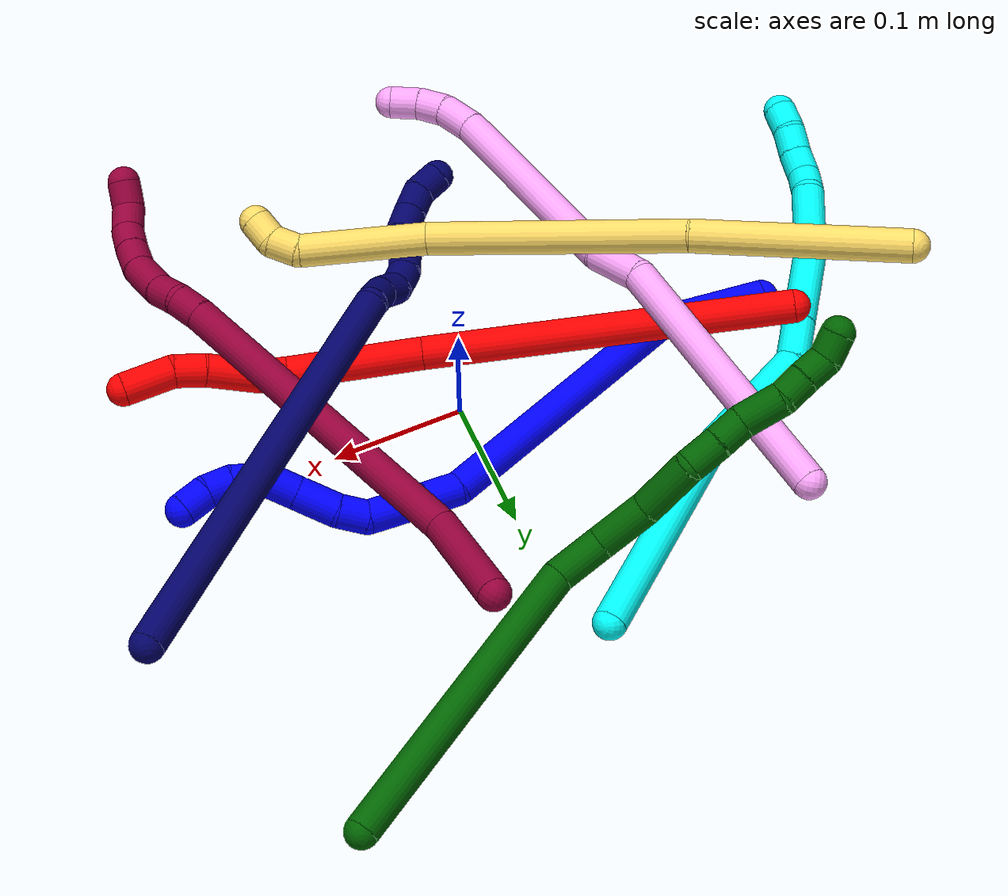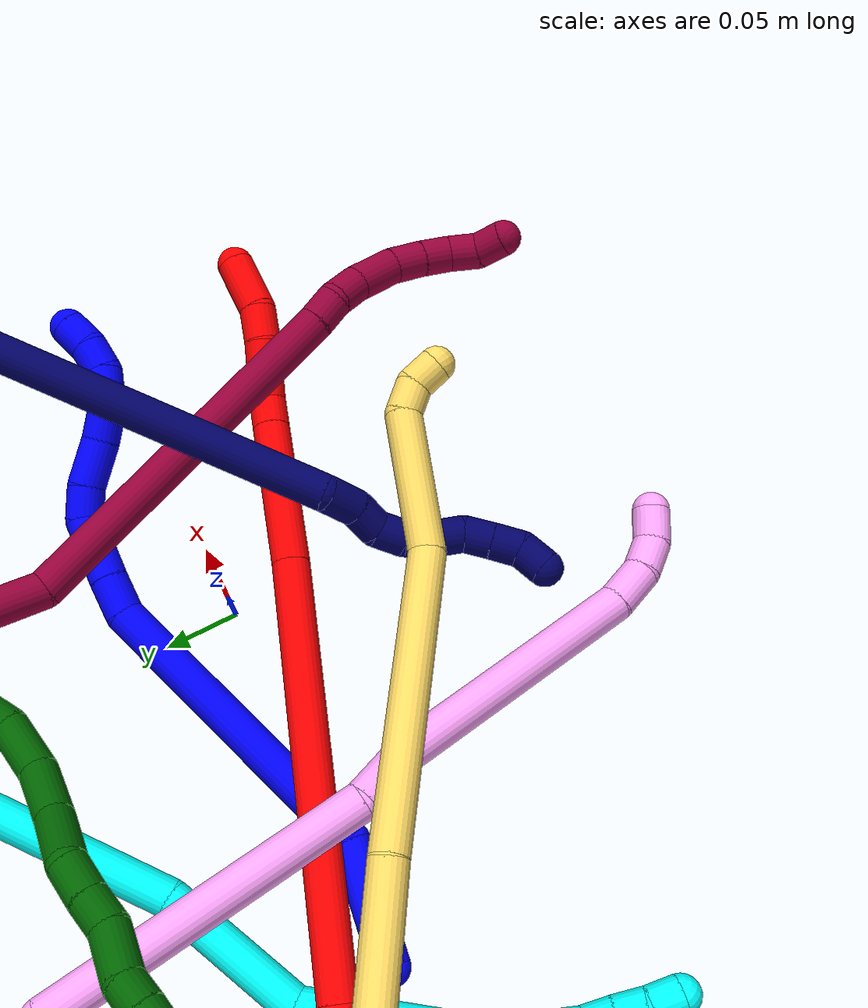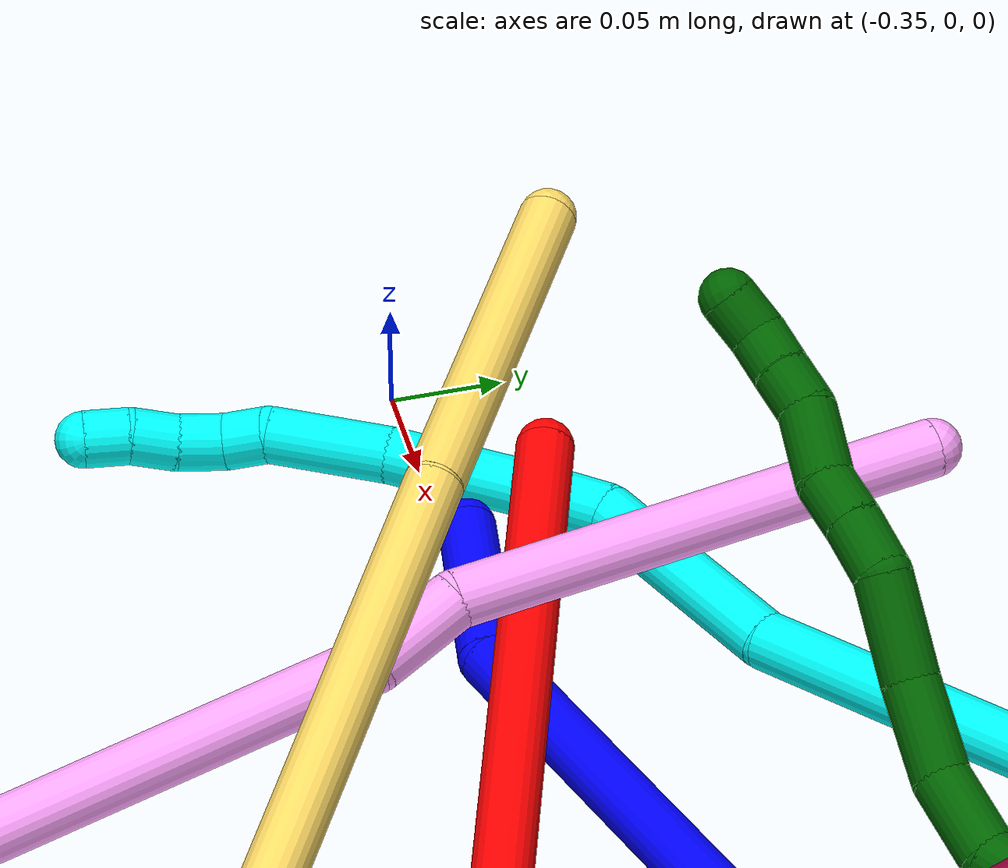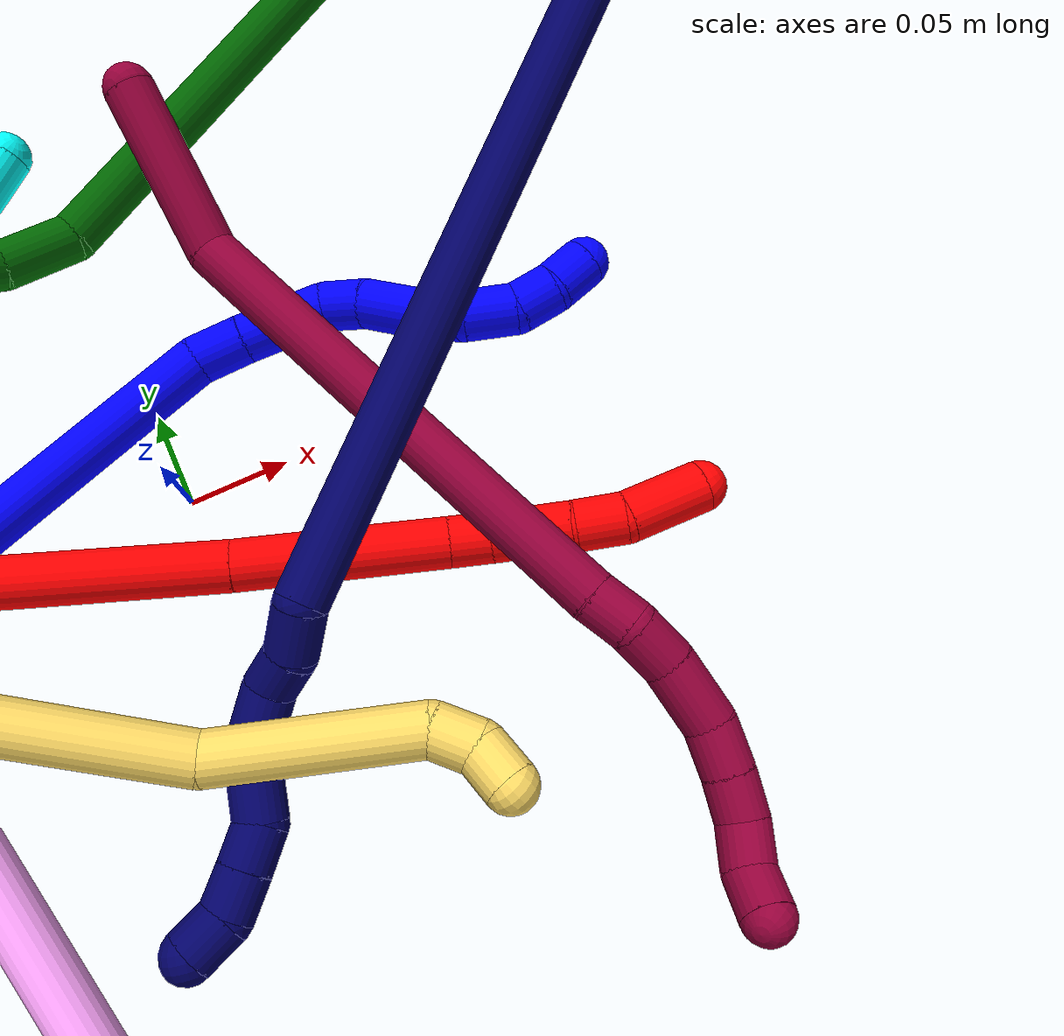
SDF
<sdf version="1.7">
 <world name="default">
  <plugin name="TubeGeneratorPlugin" filename="libtube_generator_plugin.so"/>
  <model name="photoneo_s_sensor">
   <static>1</static>
   <pose>0 0 2 1.57079 1.57079 3.14159</pose>
   <link name="link">
    <inertial><mass>0.1</mass></inertial>
    <sensor name="sensor" type="depth">
     <update_rate>30</update_rate>
     <camera>
      <horizontal_fov>1.22</horizontal_fov>
      <image><width>1920</width><height>1200</height><format>B8G8R8</format></image>
      <clip><near>0.1</near><far>4</far></clip>
      <depth_camera><output>points</output></depth_camera>
     </camera>
     <plugin name="camera_plugin" filename="libgazebo_ros_depth_camera.so">
      <baseline>0.2</baseline>
      <alwaysOn>1</alwaysOn>
      <updateRate>0.0</updateRate>
      <cameraName>camera_ir</cameraName>
      <imageTopicName>/camera/color/image_raw</imageTopicName>
      <cameraInfoTopicName>/camera/color/camera_info</cameraInfoTopicName>
      <depthImageTopicName>/camera/depth/image_raw</depthImageTopicName>
      <depthImageCameraInfoTopicName>/camera/depth/camera_info</depthImageCameraInfoTopicName>
      <pointCloudTopicName>/camera/depth/points</pointCloudTopicName>
      <frameName>fr_optical</frameName>
      <pointCloudCutoff>0.1</pointCloudCutoff>
      <pointCloudCutoffMax>2.0</pointCloudCutoffMax>
      <distortionK1>0</distortionK1>
      <distortionK2>0</distortionK2>
      <distortionK3>0</distortionK3>
      <distortionT1>0</distortionT1>
      <distortionT2>0</distortionT2>
      <CxPrime>0</CxPrime>
      <Cx>0</Cx>
      <Cy>0</Cy>
      <focalLength>0</focalLength>
      <hackBaseline>0</hackBaseline>
     </plugin>
    </sensor>
   </link>
  </model>
  <gravity>0 0 -9.8</gravity>
  <magnetic_field>6e-06 2.3e-05 -4.2e-05</magnetic_field>
  <atmosphere type="adiabatic"/>
  <physics name="default_physics" default="0" type="ode">
   <max_step_size>0.003</max_step_size>
   <real_time_factor>1</real_time_factor>
   <real_time_update_rate>1000</real_time_update_rate>
   <max_contacts>10000</max_contacts>
   <ode>
    <solver>
     <type>quick</type>
     <iters>100</iters>
     <sor>1.3</sor>
     <use_dynamic_moi_rescaling>0</use_dynamic_moi_rescaling>
    </solver>
    <constraints>
     <contact_max_correcting_vel>0</contact_max_correcting_vel>
     <contact_surface_layer>0.001</contact_surface_layer>
     <cfm>0</cfm>
     <erp>0.2</erp>
    </constraints>
   </ode>
  </physics>
  <scene><ambient>0.4 0.4 0.4 1</ambient><background>0.7 0.7 0.7 1</background><shadows>0</shadows></scene>
  <audio><device>default</device></audio>
  <spherical_coordinates>
   <surface_model>EARTH_WGS84</surface_model>
   <latitude_deg>0</latitude_deg>
   <longitude_deg>0</longitude_deg>
   <elevation>0</elevation>
   <heading_deg>0</heading_deg>
  </spherical_coordinates>
  <model name="bin">
   <static>1</static>
   <link name="bottom">
    <collision name="collision-bottom">
     <pose>0 0 -0.01 0 -0 0</pose>
     <geometry><box><size>0.8 0.6 0.02</size></box></geometry>
     <surface>
      <friction><ode><mu>100</mu><mu2>100</mu2></ode></friction>
      <contact><collide_bitmask>65535</collide_bitmask></contact>
     </surface>
    </collision>
   </link>
   <link name="west_wall">
    <collision name="collision-west_wall">
     <pose>-0.41 0 0.1 0 -0 0</pose>
     <geometry><box><size>0.02 0.6 0.2</size></box></geometry>
     <surface>
      <friction><ode><mu>100</mu><mu2>100</mu2></ode></friction>
      <contact><collide_bitmask>65535</collide_bitmask></contact>
     </surface>
    </collision>
   </link>
   <link name="east_wall">
    <collision name="collision-east_wall">
     <pose>0.41 0 0.1 0 -0 0</pose>
     <geometry><box><size>0.02 0.6 0.2</size></box></geometry>
     <surface>
      <friction><ode><mu>100</mu><mu2>100</mu2></ode></friction>
      <contact><collide_bitmask>65535</collide_bitmask></contact>
     </surface>
    </collision>
   </link>
   <link name="south_wall">
    <collision name="collision-south_wall">
     <pose>0 -0.31 0.1 0 -0 0</pose>
     <geometry><box><size>0.8 0.02 0.2</size></box></geometry>
     <surface>
      <friction><ode><mu>100</mu><mu2>100</mu2></ode></friction>
      <contact><collide_bitmask>65535</collide_bitmask></contact>
     </surface>
    </collision>
   </link>
   <link name="north_wall">
    <collision name="collision-north_wall">
     <pose>0 0.31 0.1 0 -0 0</pose>
     <geometry><box><size>0.8 0.02 0.2</size></box></geometry>
     <surface>
      <friction><ode><mu>100</mu><mu2>100</mu2></ode></friction>
      <contact><collide_bitmask>65535</collide_bitmask></contact>
     </surface>
    </collision>
   </link>
  </model>
  <model name="1">
   <static>0</static>
   <link name="1">
    <collision name="collision-cylinder-e_1_1_4">
     <pose>0.039305 0.000914 -0.004238 -2.92916 1.46095 -2.90466</pose>
     <geometry><cylinder><radius>0.0125</radius><length>0.079087</length></cylinder></geometry>
     <surface>
      <friction><ode><mu>1.16</mu><mu2>1.16</mu2><slip1>0</slip1><slip2>0</slip2></ode></friction>
      <contact><ode><kp>1e+06</kp><kd>1</kd><max_vel>0</max_vel><min_depth>0.001</min_depth></ode></contact>
     </surface>
    </collision>
    <visual name="visual-cylinder-e_1_1_4">
     <pose>0.039305 0.000914 -0.004238 -2.92916 1.46095 -2.90466</pose>
     <geometry><cylinder><radius>0.0125</radius><length>0.079087</length></cylinder></geometry>
     <material><ambient>0 0 1 1</ambient></material>
    </visual>
    <collision name="collision-cylinder-e_2_4_5">
     <pose>0.165535 0.030857 -0.057255 -2.60478 0.992293 -2.20137</pose>
     <geometry><cylinder><radius>0.0125</radius><length>0.207634</length></cylinder></geometry>
     <surface>
      <friction><ode><mu>1.16</mu><mu2>1.16</mu2><slip1>0</slip1><slip2>0</slip2></ode></friction>
      <contact><ode><kp>1e+06</kp><kd>1</kd><max_vel>0</max_vel><min_depth>0.001</min_depth></ode></contact>
     </surface>
    </collision>
    <visual name="visual-cylinder-e_2_4_5">
     <pose>0.165535 0.030857 -0.057255 -2.60478 0.992293 -2.20137</pose>
     <geometry><cylinder><radius>0.0125</radius><length>0.207634</length></cylinder></geometry>
     <material><ambient>0 0 1 1</ambient></material>
    </visual>
    <collision name="collision-cylinder-e_3_5_6">
     <pose>0.265033 0.062483 -0.108038 -2.22781 1.31566 -2.00831</pose>
     <geometry><cylinder><radius>0.0125</radius><length>0.025989</length></cylinder></geometry>
     <surface>
      <friction><ode><mu>1.16</mu><mu2>1.16</mu2><slip1>0</slip1><slip2>0</slip2></ode></friction>
      <contact><ode><kp>1e+06</kp><kd>1</kd><max_vel>0</max_vel><min_depth>0.001</min_depth></ode></contact>
     </surface>
    </collision>
    <visual name="visual-cylinder-e_3_5_6">
     <pose>0.265033 0.062483 -0.108038 -2.22781 1.31566 -2.00831</pose>
     <geometry><cylinder><radius>0.0125</radius><length>0.025989</length></cylinder></geometry>
     <material><ambient>0 0 1 1</ambient></material>
    </visual>
    <collision name="collision-cylinder-e_4_6_7">
     <pose>0.299246 0.068547 -0.113116 -2.29648 1.35983 -2.12651</pose>
     <geometry><cylinder><radius>0.0125</radius><length>0.044261</length></cylinder></geometry>
     <surface>
      <friction><ode><mu>1.16</mu><mu2>1.16</mu2><slip1>0</slip1><slip2>0</slip2></ode></friction>
      <contact><ode><kp>1e+06</kp><kd>1</kd><max_vel>0</max_vel><min_depth>0.001</min_depth></ode></contact>
     </surface>
    </collision>
    <visual name="visual-cylinder-e_4_6_7">
     <pose>0.299246 0.068547 -0.113116 -2.29648 1.35983 -2.12651</pose>
     <geometry><cylinder><radius>0.0125</radius><length>0.044261</length></cylinder></geometry>
     <material><ambient>0 0 1 1</ambient></material>
    </visual>
    <collision name="collision-cylinder-e_5_7_8">
     <pose>0.331153 0.073069 -0.112138 -0.254772 1.18338 -0.171717</pose>
     <geometry><cylinder><radius>0.0125</radius><length>0.022177</length></cylinder></geometry>
     <surface>
      <friction><ode><mu>1.16</mu><mu2>1.16</mu2><slip1>0</slip1><slip2>0</slip2></ode></friction>
      <contact><ode><kp>1e+06</kp><kd>1</kd><max_vel>0</max_vel><min_depth>0.001</min_depth></ode></contact>
     </surface>
    </collision>
    <visual name="visual-cylinder-e_5_7_8">
     <pose>0.331153 0.073069 -0.112138 -0.254772 1.18338 -0.171717</pose>
     <geometry><cylinder><radius>0.0125</radius><length>0.022177</length></cylinder></geometry>
     <material><ambient>0 0 1 1</ambient></material>
    </visual>
    <collision name="collision-cylinder-e_6_8_9">
     <pose>0.3549 0.073314 -0.099498 0.094126 1.00168 0.051551</pose>
     <geometry><cylinder><radius>0.0125</radius><length>0.032005</length></cylinder></geometry>
     <surface>
      <friction><ode><mu>1.16</mu><mu2>1.16</mu2><slip1>0</slip1><slip2>0</slip2></ode></friction>
      <contact><ode><kp>1e+06</kp><kd>1</kd><max_vel>0</max_vel><min_depth>0.001</min_depth></ode></contact>
     </surface>
    </collision>
    <visual name="visual-cylinder-e_6_8_9">
     <pose>0.3549 0.073314 -0.099498 0.094126 1.00168 0.051551</pose>
     <geometry><cylinder><radius>0.0125</radius><length>0.032005</length></cylinder></geometry>
     <material><ambient>0 0 1 1</ambient></material>
    </visual>
    <collision name="collision-cylinder-e_7_9_10">
     <pose>0.377677 0.073581 -0.084955 -0.178872 0.993569 -0.097156</pose>
     <geometry><cylinder><radius>0.0125</radius><length>0.022189</length></cylinder></geometry>
     <surface>
      <friction><ode><mu>1.16</mu><mu2>1.16</mu2><slip1>0</slip1><slip2>0</slip2></ode></friction>
      <contact><ode><kp>1e+06</kp><kd>1</kd><max_vel>0</max_vel><min_depth>0.001</min_depth></ode></contact>
     </surface>
    </collision>
    <visual name="visual-cylinder-e_7_9_10">
     <pose>0.377677 0.073581 -0.084955 -0.178872 0.993569 -0.097156</pose>
     <geometry><cylinder><radius>0.0125</radius><length>0.022189</length></cylinder></geometry>
     <material><ambient>0 0 1 1</ambient></material>
    </visual>
    <collision name="collision-cylinder-e_8_10_11">
     <pose>0.399832 0.07488 -0.077723 -0.172226 1.47056 -0.155843</pose>
     <geometry><cylinder><radius>0.0125</radius><length>0.025846</length></cylinder></geometry>
     <surface>
      <friction><ode><mu>1.16</mu><mu2>1.16</mu2><slip1>0</slip1><slip2>0</slip2></ode></friction>
      <contact><ode><kp>1e+06</kp><kd>1</kd><max_vel>0</max_vel><min_depth>0.001</min_depth></ode></contact>
     </surface>
    </collision>
    <visual name="visual-cylinder-e_8_10_11">
     <pose>0.399832 0.07488 -0.077723 -0.172226 1.47056 -0.155843</pose>
     <geometry><cylinder><radius>0.0125</radius><length>0.025846</length></cylinder></geometry>
     <material><ambient>0 0 1 1</ambient></material>
    </visual>
    <collision name="collision-cylinder-e_9_11_12">
     <pose>0.422193 0.077681 -0.078701 -2.28862 1.22495 -1.99349</pose>
     <geometry><cylinder><radius>0.0125</radius><length>0.020202</length></cylinder></geometry>
     <surface>
      <friction><ode><mu>1.16</mu><mu2>1.16</mu2><slip1>0</slip1><slip2>0</slip2></ode></friction>
      <contact><ode><kp>1e+06</kp><kd>1</kd><max_vel>0</max_vel><min_depth>0.001</min_depth></ode></contact>
     </surface>
    </collision>
    <visual name="visual-cylinder-e_9_11_12">
     <pose>0.422193 0.077681 -0.078701 -2.28862 1.22495 -1.99349</pose>
     <geometry><cylinder><radius>0.0125</radius><length>0.020202</length></cylinder></geometry>
     <material><ambient>0 0 1 1</ambient></material>
    </visual>
    <collision name="collision-cylinder-e_10_12_2">
     <pose>0.440429 0.082904 -0.085742 -2.63698 1.01128 -2.27003</pose>
     <geometry><cylinder><radius>0.0125</radius><length>0.02061</length></cylinder></geometry>
     <surface>
      <friction><ode><mu>1.16</mu><mu2>1.16</mu2><slip1>0</slip1><slip2>0</slip2></ode></friction>
      <contact><ode><kp>1e+06</kp><kd>1</kd><max_vel>0</max_vel><min_depth>0.001</min_depth></ode></contact>
     </surface>
    </collision>
    <visual name="visual-cylinder-e_10_12_2">
     <pose>0.440429 0.082904 -0.085742 -2.63698 1.01128 -2.27003</pose>
     <geometry><cylinder><radius>0.0125</radius><length>0.02061</length></cylinder></geometry>
     <material><ambient>0 0 1 1</ambient></material>
    </visual>
    <collision name="collision-sphere-2">
     <pose>0.449163 0.085549 -0.090529 0 -0 0</pose>
     <geometry><sphere><radius>0.0125</radius></sphere></geometry>
     <surface>
      <friction><ode><mu>1.16</mu><mu2>1.16</mu2><slip1>0</slip1><slip2>0</slip2></ode></friction>
      <contact><ode><kp>1e+06</kp><kd>1</kd><max_vel>0</max_vel><min_depth>0.001</min_depth></ode></contact>
     </surface>
    </collision>
    <visual name="visual-sphere-2">
     <pose>0.449163 0.085549 -0.090529 0 -0 0</pose>
     <geometry><sphere><radius>0.0125</radius></sphere></geometry>
     <material><ambient>0 0 1 1</ambient></material>
    </visual>
    <collision name="collision-sphere-12">
     <pose>0.431696 0.08026 -0.080954 0 -0 0</pose>
     <geometry><sphere><radius>0.0125</radius></sphere></geometry>
     <surface>
      <friction><ode><mu>1.16</mu><mu2>1.16</mu2><slip1>0</slip1><slip2>0</slip2></ode></friction>
      <contact><ode><kp>1e+06</kp><kd>1</kd><max_vel>0</max_vel><min_depth>0.001</min_depth></ode></contact>
     </surface>
    </collision>
    <visual name="visual-sphere-12">
     <pose>0.431696 0.08026 -0.080954 0 -0 0</pose>
     <geometry><sphere><radius>0.0125</radius></sphere></geometry>
     <material><ambient>0 0 1 1</ambient></material>
    </visual>
    <collision name="collision-sphere-11">
     <pose>0.41269 0.075101 -0.076449 0 -0 0</pose>
     <geometry><sphere><radius>0.0125</radius></sphere></geometry>
     <surface>
      <friction><ode><mu>1.16</mu><mu2>1.16</mu2><slip1>0</slip1><slip2>0</slip2></ode></friction>
      <contact><ode><kp>1e+06</kp><kd>1</kd><max_vel>0</max_vel><min_depth>0.001</min_depth></ode></contact>
     </surface>
    </collision>
    <visual name="visual-sphere-11">
     <pose>0.41269 0.075101 -0.076449 0 -0 0</pose>
     <geometry><sphere><radius>0.0125</radius></sphere></geometry>
     <material><ambient>0 0 1 1</ambient></material>
    </visual>
    <collision name="collision-sphere-10">
     <pose>0.386974 0.074658 -0.078997 0 -0 0</pose>
     <geometry><sphere><radius>0.0125</radius></sphere></geometry>
     <surface>
      <friction><ode><mu>1.16</mu><mu2>1.16</mu2><slip1>0</slip1><slip2>0</slip2></ode></friction>
      <contact><ode><kp>1e+06</kp><kd>1</kd><max_vel>0</max_vel><min_depth>0.001</min_depth></ode></contact>
     </surface>
    </collision>
    <visual name="visual-sphere-10">
     <pose>0.386974 0.074658 -0.078997 0 -0 0</pose>
     <geometry><sphere><radius>0.0125</radius></sphere></geometry>
     <material><ambient>0 0 1 1</ambient></material>
    </visual>
    <collision name="collision-sphere-9">
     <pose>0.36838 0.072504 -0.090913 0 -0 0</pose>
     <geometry><sphere><radius>0.0125</radius></sphere></geometry>
     <surface>
      <friction><ode><mu>1.16</mu><mu2>1.16</mu2><slip1>0</slip1><slip2>0</slip2></ode></friction>
      <contact><ode><kp>1e+06</kp><kd>1</kd><max_vel>0</max_vel><min_depth>0.001</min_depth></ode></contact>
     </surface>
    </collision>
    <visual name="visual-sphere-9">
     <pose>0.36838 0.072504 -0.090913 0 -0 0</pose>
     <geometry><sphere><radius>0.0125</radius></sphere></geometry>
     <material><ambient>0 0 1 1</ambient></material>
    </visual>
    <collision name="collision-sphere-4">
     <pose>0.07861 0.001828 -0.008475 0 -0 0</pose>
     <geometry><sphere><radius>0.0125</radius></sphere></geometry>
     <surface>
      <friction><ode><mu>1.16</mu><mu2>1.16</mu2><slip1>0</slip1><slip2>0</slip2></ode></friction>
      <contact><ode><kp>1e+06</kp><kd>1</kd><max_vel>0</max_vel><min_depth>0.001</min_depth></ode></contact>
     </surface>
    </collision>
    <visual name="visual-sphere-4">
     <pose>0.07861 0.001828 -0.008475 0 -0 0</pose>
     <geometry><sphere><radius>0.0125</radius></sphere></geometry>
     <material><ambient>0 0 1 1</ambient></material>
    </visual>
    <collision name="collision-sphere-1">
     <geometry><sphere><radius>0.0125</radius></sphere></geometry>
     <surface>
      <friction><ode><mu>1.16</mu><mu2>1.16</mu2><slip1>0</slip1><slip2>0</slip2></ode></friction>
      <contact><ode><kp>1e+06</kp><kd>1</kd><max_vel>0</max_vel><min_depth>0.001</min_depth></ode></contact>
     </surface>
    </collision>
    <visual name="visual-sphere-1">
     <geometry><sphere><radius>0.0125</radius></sphere></geometry>
     <material><ambient>0 0 1 1</ambient></material>
    </visual>
    <collision name="collision-sphere-8">
     <pose>0.34142 0.074125 -0.108084 0 -0 0</pose>
     <geometry><sphere><radius>0.0125</radius></sphere></geometry>
     <surface>
      <friction><ode><mu>1.16</mu><mu2>1.16</mu2><slip1>0</slip1><slip2>0</slip2></ode></friction>
      <contact><ode><kp>1e+06</kp><kd>1</kd><max_vel>0</max_vel><min_depth>0.001</min_depth></ode></contact>
     </surface>
    </collision>
    <visual name="visual-sphere-8">
     <pose>0.34142 0.074125 -0.108084 0 -0 0</pose>
     <geometry><sphere><radius>0.0125</radius></sphere></geometry>
     <material><ambient>0 0 1 1</ambient></material>
    </visual>
    <collision name="collision-sphere-5">
     <pose>0.252459 0.059887 -0.106035 0 -0 0</pose>
     <geometry><sphere><radius>0.0125</radius></sphere></geometry>
     <surface>
      <friction><ode><mu>1.16</mu><mu2>1.16</mu2><slip1>0</slip1><slip2>0</slip2></ode></friction>
      <contact><ode><kp>1e+06</kp><kd>1</kd><max_vel>0</max_vel><min_depth>0.001</min_depth></ode></contact>
     </surface>
    </collision>
    <visual name="visual-sphere-5">
     <pose>0.252459 0.059887 -0.106035 0 -0 0</pose>
     <geometry><sphere><radius>0.0125</radius></sphere></geometry>
     <material><ambient>0 0 1 1</ambient></material>
    </visual>
    <collision name="collision-sphere-6">
     <pose>0.277606 0.06508 -0.110041 0 -0 0</pose>
     <geometry><sphere><radius>0.0125</radius></sphere></geometry>
     <surface>
      <friction><ode><mu>1.16</mu><mu2>1.16</mu2><slip1>0</slip1><slip2>0</slip2></ode></friction>
      <contact><ode><kp>1e+06</kp><kd>1</kd><max_vel>0</max_vel><min_depth>0.001</min_depth></ode></contact>
     </surface>
    </collision>
    <visual name="visual-sphere-6">
     <pose>0.277606 0.06508 -0.110041 0 -0 0</pose>
     <geometry><sphere><radius>0.0125</radius></sphere></geometry>
     <material><ambient>0 0 1 1</ambient></material>
    </visual>
    <collision name="collision-sphere-7">
     <pose>0.320886 0.072013 -0.116192 0 -0 0</pose>
     <geometry><sphere><radius>0.0125</radius></sphere></geometry>
     <surface>
      <friction><ode><mu>1.16</mu><mu2>1.16</mu2><slip1>0</slip1><slip2>0</slip2></ode></friction>
      <contact><ode><kp>1e+06</kp><kd>1</kd><max_vel>0</max_vel><min_depth>0.001</min_depth></ode></contact>
     </surface>
    </collision>
    <visual name="visual-sphere-7">
     <pose>0.320886 0.072013 -0.116192 0 -0 0</pose>
     <geometry><sphere><radius>0.0125</radius></sphere></geometry>
     <material><ambient>0 0 1 1</ambient></material>
    </visual>
    <inertial>
     <pose>0.22527 0.0439 -0.06592 0 -0 0</pose>
     <mass>0.5</mass>
     <inertia>
      <ixx>-0.000548</ixx>
      <ixy>0</ixy>
      <ixz>0</ixz>
      <iyy>0.00038</iyy>
      <iyz>0</iyz>
      <izz>-0.00092</izz>
     </inertia>
    </inertial>
   </link>
   <pose>-0.244697 0.007707 0.014079 1.02993 -0.002655 -0.242627</pose>
  </model>
  <model name="2">
   <static>0</static>
   <link name="2">
    <collision name="collision-cylinder-e_1_1_4">
     <pose>0.073296 -0.02538 0.113737 0.219545 0.561443 0.063537</pose>
     <geometry><cylinder><radius>0.0125</radius><length>0.275336</length></cylinder></geometry>
     <surface>
      <friction><ode><mu>1.16</mu><mu2>1.16</mu2><slip1>0</slip1><slip2>0</slip2></ode></friction>
      <contact><ode><kp>1e+06</kp><kd>1</kd><max_vel>0</max_vel><min_depth>0.001</min_depth></ode></contact>
     </surface>
    </collision>
    <visual name="visual-cylinder-e_1_1_4">
     <pose>0.073296 -0.02538 0.113737 0.219545 0.561443 0.063537</pose>
     <geometry><cylinder><radius>0.0125</radius><length>0.275336</length></cylinder></geometry>
     <material><ambient>1 0 0 1</ambient></material>
    </visual>
    <collision name="collision-cylinder-e_2_4_5">
     <pose>0.172251 -0.058909 0.270017 0.189282 0.534796 0.051999</pose>
     <geometry><cylinder><radius>0.0125</radius><length>0.100692</length></cylinder></geometry>
     <surface>
      <friction><ode><mu>1.16</mu><mu2>1.16</mu2><slip1>0</slip1><slip2>0</slip2></ode></friction>
      <contact><ode><kp>1e+06</kp><kd>1</kd><max_vel>0</max_vel><min_depth>0.001</min_depth></ode></contact>
     </surface>
    </collision>
    <visual name="visual-cylinder-e_2_4_5">
     <pose>0.172251 -0.058909 0.270017 0.189282 0.534796 0.051999</pose>
     <geometry><cylinder><radius>0.0125</radius><length>0.100692</length></cylinder></geometry>
     <material><ambient>1 0 0 1</ambient></material>
    </visual>
    <collision name="collision-cylinder-e_3_5_6">
     <pose>0.20289 -0.069063 0.321674 0.216409 0.490189 0.054328</pose>
     <geometry><cylinder><radius>0.0125</radius><length>0.021155</length></cylinder></geometry>
     <surface>
      <friction><ode><mu>1.16</mu><mu2>1.16</mu2><slip1>0</slip1><slip2>0</slip2></ode></friction>
      <contact><ode><kp>1e+06</kp><kd>1</kd><max_vel>0</max_vel><min_depth>0.001</min_depth></ode></contact>
     </surface>
    </collision>
    <visual name="visual-cylinder-e_3_5_6">
     <pose>0.20289 -0.069063 0.321674 0.216409 0.490189 0.054328</pose>
     <geometry><cylinder><radius>0.0125</radius><length>0.021155</length></cylinder></geometry>
     <material><ambient>1 0 0 1</ambient></material>
    </visual>
    <collision name="collision-cylinder-e_4_6_7">
     <pose>0.212327 -0.078732 0.348992 0.39856 0.221919 0.044996</pose>
     <geometry><cylinder><radius>0.0125</radius><length>0.040496</length></cylinder></geometry>
     <surface>
      <friction><ode><mu>1.16</mu><mu2>1.16</mu2><slip1>0</slip1><slip2>0</slip2></ode></friction>
      <contact><ode><kp>1e+06</kp><kd>1</kd><max_vel>0</max_vel><min_depth>0.001</min_depth></ode></contact>
     </surface>
    </collision>
    <visual name="visual-cylinder-e_4_6_7">
     <pose>0.212327 -0.078732 0.348992 0.39856 0.221919 0.044996</pose>
     <geometry><cylinder><radius>0.0125</radius><length>0.040496</length></cylinder></geometry>
     <material><ambient>1 0 0 1</ambient></material>
    </visual>
    <collision name="collision-cylinder-e_5_7_8">
     <pose>0.220688 -0.089386 0.377878 0.272747 0.33844 0.046882</pose>
     <geometry><cylinder><radius>0.0125</radius><length>0.023521</length></cylinder></geometry>
     <surface>
      <friction><ode><mu>1.16</mu><mu2>1.16</mu2><slip1>0</slip1><slip2>0</slip2></ode></friction>
      <contact><ode><kp>1e+06</kp><kd>1</kd><max_vel>0</max_vel><min_depth>0.001</min_depth></ode></contact>
     </surface>
    </collision>
    <visual name="visual-cylinder-e_5_7_8">
     <pose>0.220688 -0.089386 0.377878 0.272747 0.33844 0.046882</pose>
     <geometry><cylinder><radius>0.0125</radius><length>0.023521</length></cylinder></geometry>
     <material><ambient>1 0 0 1</ambient></material>
    </visual>
    <collision name="collision-cylinder-e_6_8_2">
     <pose>0.231583 -0.091147 0.406617 -0.067879 0.368609 -0.012659</pose>
     <geometry><cylinder><radius>0.0125</radius><length>0.0388</length></cylinder></geometry>
     <surface>
      <friction><ode><mu>1.16</mu><mu2>1.16</mu2><slip1>0</slip1><slip2>0</slip2></ode></friction>
      <contact><ode><kp>1e+06</kp><kd>1</kd><max_vel>0</max_vel><min_depth>0.001</min_depth></ode></contact>
     </surface>
    </collision>
    <visual name="visual-cylinder-e_6_8_2">
     <pose>0.231583 -0.091147 0.406617 -0.067879 0.368609 -0.012659</pose>
     <geometry><cylinder><radius>0.0125</radius><length>0.0388</length></cylinder></geometry>
     <material><ambient>1 0 0 1</ambient></material>
    </visual>
    <collision name="collision-sphere-2">
     <pose>0.238573 -0.089919 0.424672 0 -0 0</pose>
     <geometry><sphere><radius>0.0125</radius></sphere></geometry>
     <surface>
      <friction><ode><mu>1.16</mu><mu2>1.16</mu2><slip1>0</slip1><slip2>0</slip2></ode></friction>
      <contact><ode><kp>1e+06</kp><kd>1</kd><max_vel>0</max_vel><min_depth>0.001</min_depth></ode></contact>
     </surface>
    </collision>
    <visual name="visual-sphere-2">
     <pose>0.238573 -0.089919 0.424672 0 -0 0</pose>
     <geometry><sphere><radius>0.0125</radius></sphere></geometry>
     <material><ambient>1 0 0 1</ambient></material>
    </visual>
    <collision name="collision-sphere-4">
     <pose>0.146591 -0.050759 0.227474 0 -0 0</pose>
     <geometry><sphere><radius>0.0125</radius></sphere></geometry>
     <surface>
      <friction><ode><mu>1.16</mu><mu2>1.16</mu2><slip1>0</slip1><slip2>0</slip2></ode></friction>
      <contact><ode><kp>1e+06</kp><kd>1</kd><max_vel>0</max_vel><min_depth>0.001</min_depth></ode></contact>
     </surface>
    </collision>
    <visual name="visual-sphere-4">
     <pose>0.146591 -0.050759 0.227474 0 -0 0</pose>
     <geometry><sphere><radius>0.0125</radius></sphere></geometry>
     <material><ambient>1 0 0 1</ambient></material>
    </visual>
    <collision name="collision-sphere-1">
     <geometry><sphere><radius>0.0125</radius></sphere></geometry>
     <surface>
      <friction><ode><mu>1.16</mu><mu2>1.16</mu2><slip1>0</slip1><slip2>0</slip2></ode></friction>
      <contact><ode><kp>1e+06</kp><kd>1</kd><max_vel>0</max_vel><min_depth>0.001</min_depth></ode></contact>
     </surface>
    </collision>
    <visual name="visual-sphere-1">
     <geometry><sphere><radius>0.0125</radius></sphere></geometry>
     <material><ambient>1 0 0 1</ambient></material>
    </visual>
    <collision name="collision-sphere-8">
     <pose>0.224593 -0.092374 0.388562 0 -0 0</pose>
     <geometry><sphere><radius>0.0125</radius></sphere></geometry>
     <surface>
      <friction><ode><mu>1.16</mu><mu2>1.16</mu2><slip1>0</slip1><slip2>0</slip2></ode></friction>
      <contact><ode><kp>1e+06</kp><kd>1</kd><max_vel>0</max_vel><min_depth>0.001</min_depth></ode></contact>
     </surface>
    </collision>
    <visual name="visual-sphere-8">
     <pose>0.224593 -0.092374 0.388562 0 -0 0</pose>
     <geometry><sphere><radius>0.0125</radius></sphere></geometry>
     <material><ambient>1 0 0 1</ambient></material>
    </visual>
    <collision name="collision-sphere-5">
     <pose>0.197911 -0.067059 0.31256 0 -0 0</pose>
     <geometry><sphere><radius>0.0125</radius></sphere></geometry>
     <surface>
      <friction><ode><mu>1.16</mu><mu2>1.16</mu2><slip1>0</slip1><slip2>0</slip2></ode></friction>
      <contact><ode><kp>1e+06</kp><kd>1</kd><max_vel>0</max_vel><min_depth>0.001</min_depth></ode></contact>
     </surface>
    </collision>
    <visual name="visual-sphere-5">
     <pose>0.197911 -0.067059 0.31256 0 -0 0</pose>
     <geometry><sphere><radius>0.0125</radius></sphere></geometry>
     <material><ambient>1 0 0 1</ambient></material>
    </visual>
    <collision name="collision-sphere-6">
     <pose>0.20787 -0.071067 0.330788 0 -0 0</pose>
     <geometry><sphere><radius>0.0125</radius></sphere></geometry>
     <surface>
      <friction><ode><mu>1.16</mu><mu2>1.16</mu2><slip1>0</slip1><slip2>0</slip2></ode></friction>
      <contact><ode><kp>1e+06</kp><kd>1</kd><max_vel>0</max_vel><min_depth>0.001</min_depth></ode></contact>
     </surface>
    </collision>
    <visual name="visual-sphere-6">
     <pose>0.20787 -0.071067 0.330788 0 -0 0</pose>
     <geometry><sphere><radius>0.0125</radius></sphere></geometry>
     <material><ambient>1 0 0 1</ambient></material>
    </visual>
    <collision name="collision-sphere-7">
     <pose>0.216783 -0.086398 0.367195 0 -0 0</pose>
     <geometry><sphere><radius>0.0125</radius></sphere></geometry>
     <surface>
      <friction><ode><mu>1.16</mu><mu2>1.16</mu2><slip1>0</slip1><slip2>0</slip2></ode></friction>
      <contact><ode><kp>1e+06</kp><kd>1</kd><max_vel>0</max_vel><min_depth>0.001</min_depth></ode></contact>
     </surface>
    </collision>
    <visual name="visual-sphere-7">
     <pose>0.216783 -0.086398 0.367195 0 -0 0</pose>
     <geometry><sphere><radius>0.0125</radius></sphere></geometry>
     <material><ambient>1 0 0 1</ambient></material>
    </visual>
    <inertial>
     <pose>0.129184 -0.046416 0.208214 0 -0 0</pose>
     <mass>0.5</mass>
     <inertia>
      <ixx>0.001688</ixx>
      <ixy>0</ixy>
      <ixz>0</ixz>
      <iyy>0.001913</iyy>
      <iyz>0</iyz>
      <izz>-0.000609</izz>
     </inertia>
    </inertial>
   </link>
   <pose>-0.249683 0.043191 0.046914 -0.930798 0.993985 -0.920199</pose>
  </model>
  <model name="3">
   <static>0</static>
   <link name="3">
    <collision name="collision-cylinder-e_1_1_4">
     <pose>0.021013 -0.04843 -0.062774 2.48447 0.259076 0.729975</pose>
     <geometry><cylinder><radius>0.0125</radius><length>0.164044</length></cylinder></geometry>
     <surface>
      <friction><ode><mu>1.16</mu><mu2>1.16</mu2><slip1>0</slip1><slip2>0</slip2></ode></friction>
      <contact><ode><kp>1e+06</kp><kd>1</kd><max_vel>0</max_vel><min_depth>0.001</min_depth></ode></contact>
     </surface>
    </collision>
    <visual name="visual-cylinder-e_1_1_4">
     <pose>0.021013 -0.04843 -0.062774 2.48447 0.259076 0.729975</pose>
     <geometry><cylinder><radius>0.0125</radius><length>0.164044</length></cylinder></geometry>
     <material><ambient>0.003922 1 0.996078 1</ambient></material>
    </visual>
    <collision name="collision-cylinder-e_2_4_5">
     <pose>0.042172 -0.128457 -0.164633 2.46175 0.002906 0.008218</pose>
     <geometry><cylinder><radius>0.0125</radius><length>0.10052</length></cylinder></geometry>
     <surface>
      <friction><ode><mu>1.16</mu><mu2>1.16</mu2><slip1>0</slip1><slip2>0</slip2></ode></friction>
      <contact><ode><kp>1e+06</kp><kd>1</kd><max_vel>0</max_vel><min_depth>0.001</min_depth></ode></contact>
     </surface>
    </collision>
    <visual name="visual-cylinder-e_2_4_5">
     <pose>0.042172 -0.128457 -0.164633 2.46175 0.002906 0.008218</pose>
     <geometry><cylinder><radius>0.0125</radius><length>0.10052</length></cylinder></geometry>
     <material><ambient>0.003922 1 0.996078 1</ambient></material>
    </visual>
    <collision name="collision-cylinder-e_3_5_6">
     <pose>0.050192 -0.171664 -0.213114 2.25117 0.485156 0.956814</pose>
     <geometry><cylinder><radius>0.0125</radius><length>0.033767</length></cylinder></geometry>
     <surface>
      <friction><ode><mu>1.16</mu><mu2>1.16</mu2><slip1>0</slip1><slip2>0</slip2></ode></friction>
      <contact><ode><kp>1e+06</kp><kd>1</kd><max_vel>0</max_vel><min_depth>0.001</min_depth></ode></contact>
     </surface>
    </collision>
    <visual name="visual-cylinder-e_3_5_6">
     <pose>0.050192 -0.171664 -0.213114 2.25117 0.485156 0.956814</pose>
     <geometry><cylinder><radius>0.0125</radius><length>0.033767</length></cylinder></geometry>
     <material><ambient>0.003922 1 0.996078 1</ambient></material>
    </visual>
    <collision name="collision-cylinder-e_4_6_7">
     <pose>0.073931 -0.204557 -0.242136 2.31569 0.501311 1.0577</pose>
     <geometry><cylinder><radius>0.0125</radius><length>0.066027</length></cylinder></geometry>
     <surface>
      <friction><ode><mu>1.16</mu><mu2>1.16</mu2><slip1>0</slip1><slip2>0</slip2></ode></friction>
      <contact><ode><kp>1e+06</kp><kd>1</kd><max_vel>0</max_vel><min_depth>0.001</min_depth></ode></contact>
     </surface>
    </collision>
    <visual name="visual-cylinder-e_4_6_7">
     <pose>0.073931 -0.204557 -0.242136 2.31569 0.501311 1.0577</pose>
     <geometry><cylinder><radius>0.0125</radius><length>0.066027</length></cylinder></geometry>
     <material><ambient>0.003922 1 0.996078 1</ambient></material>
    </visual>
    <collision name="collision-cylinder-e_5_7_8">
     <pose>0.105818 -0.243698 -0.273757 2.16232 0.640174 1.1129</pose>
     <geometry><cylinder><radius>0.0125</radius><length>0.053646</length></cylinder></geometry>
     <surface>
      <friction><ode><mu>1.16</mu><mu2>1.16</mu2><slip1>0</slip1><slip2>0</slip2></ode></friction>
      <contact><ode><kp>1e+06</kp><kd>1</kd><max_vel>0</max_vel><min_depth>0.001</min_depth></ode></contact>
     </surface>
    </collision>
    <visual name="visual-cylinder-e_5_7_8">
     <pose>0.105818 -0.243698 -0.273757 2.16232 0.640174 1.1129</pose>
     <geometry><cylinder><radius>0.0125</radius><length>0.053646</length></cylinder></geometry>
     <material><ambient>0.003922 1 0.996078 1</ambient></material>
    </visual>
    <collision name="collision-cylinder-e_6_8_9">
     <pose>0.129177 -0.265095 -0.291609 2.59789 0.820113 2.00118</pose>
     <geometry><cylinder><radius>0.0125</radius><length>0.020064</length></cylinder></geometry>
     <surface>
      <friction><ode><mu>1.16</mu><mu2>1.16</mu2><slip1>0</slip1><slip2>0</slip2></ode></friction>
      <contact><ode><kp>1e+06</kp><kd>1</kd><max_vel>0</max_vel><min_depth>0.001</min_depth></ode></contact>
     </surface>
    </collision>
    <visual name="visual-cylinder-e_6_8_9">
     <pose>0.129177 -0.265095 -0.291609 2.59789 0.820113 2.00118</pose>
     <geometry><cylinder><radius>0.0125</radius><length>0.020064</length></cylinder></geometry>
     <material><ambient>0.003922 1 0.996078 1</ambient></material>
    </visual>
    <collision name="collision-cylinder-e_7_9_10">
     <pose>0.144701 -0.274736 -0.300024 1.96788 0.891288 1.24584</pose>
     <geometry><cylinder><radius>0.0125</radius><length>0.021053</length></cylinder></geometry>
     <surface>
      <friction><ode><mu>1.16</mu><mu2>1.16</mu2><slip1>0</slip1><slip2>0</slip2></ode></friction>
      <contact><ode><kp>1e+06</kp><kd>1</kd><max_vel>0</max_vel><min_depth>0.001</min_depth></ode></contact>
     </surface>
    </collision>
    <visual name="visual-cylinder-e_7_9_10">
     <pose>0.144701 -0.274736 -0.300024 1.96788 0.891288 1.24584</pose>
     <geometry><cylinder><radius>0.0125</radius><length>0.021053</length></cylinder></geometry>
     <material><ambient>0.003922 1 0.996078 1</ambient></material>
    </visual>
    <collision name="collision-cylinder-e_8_10_11">
     <pose>0.159927 -0.288194 -0.30434 1.80531 0.749244 0.9244</pose>
     <geometry><cylinder><radius>0.0125</radius><length>0.020665</length></cylinder></geometry>
     <surface>
      <friction><ode><mu>1.16</mu><mu2>1.16</mu2><slip1>0</slip1><slip2>0</slip2></ode></friction>
      <contact><ode><kp>1e+06</kp><kd>1</kd><max_vel>0</max_vel><min_depth>0.001</min_depth></ode></contact>
     </surface>
    </collision>
    <visual name="visual-cylinder-e_8_10_11">
     <pose>0.159927 -0.288194 -0.30434 1.80531 0.749244 0.9244</pose>
     <geometry><cylinder><radius>0.0125</radius><length>0.020665</length></cylinder></geometry>
     <material><ambient>0.003922 1 0.996078 1</ambient></material>
    </visual>
    <collision name="collision-cylinder-e_9_11_2">
     <pose>0.175163 -0.300951 -0.308504 1.9901 0.946205 1.33548</pose>
     <geometry><cylinder><radius>0.0125</radius><length>0.020213</length></cylinder></geometry>
     <surface>
      <friction><ode><mu>1.16</mu><mu2>1.16</mu2><slip1>0</slip1><slip2>0</slip2></ode></friction>
      <contact><ode><kp>1e+06</kp><kd>1</kd><max_vel>0</max_vel><min_depth>0.001</min_depth></ode></contact>
     </surface>
    </collision>
    <visual name="visual-cylinder-e_9_11_2">
     <pose>0.175163 -0.300951 -0.308504 1.9901 0.946205 1.33548</pose>
     <geometry><cylinder><radius>0.0125</radius><length>0.020213</length></cylinder></geometry>
     <material><ambient>0.003922 1 0.996078 1</ambient></material>
    </visual>
    <collision name="collision-sphere-2">
     <pose>0.183361 -0.306349 -0.31091 0 -0 0</pose>
     <geometry><sphere><radius>0.0125</radius></sphere></geometry>
     <surface>
      <friction><ode><mu>1.16</mu><mu2>1.16</mu2><slip1>0</slip1><slip2>0</slip2></ode></friction>
      <contact><ode><kp>1e+06</kp><kd>1</kd><max_vel>0</max_vel><min_depth>0.001</min_depth></ode></contact>
     </surface>
    </collision>
    <visual name="visual-sphere-2">
     <pose>0.183361 -0.306349 -0.31091 0 -0 0</pose>
     <geometry><sphere><radius>0.0125</radius></sphere></geometry>
     <material><ambient>0.003922 1 0.996078 1</ambient></material>
    </visual>
    <collision name="collision-sphere-11">
     <pose>0.166964 -0.295553 -0.306098 0 -0 0</pose>
     <geometry><sphere><radius>0.0125</radius></sphere></geometry>
     <surface>
      <friction><ode><mu>1.16</mu><mu2>1.16</mu2><slip1>0</slip1><slip2>0</slip2></ode></friction>
      <contact><ode><kp>1e+06</kp><kd>1</kd><max_vel>0</max_vel><min_depth>0.001</min_depth></ode></contact>
     </surface>
    </collision>
    <visual name="visual-sphere-11">
     <pose>0.166964 -0.295553 -0.306098 0 -0 0</pose>
     <geometry><sphere><radius>0.0125</radius></sphere></geometry>
     <material><ambient>0.003922 1 0.996078 1</ambient></material>
    </visual>
    <collision name="collision-sphere-10">
     <pose>0.152889 -0.280836 -0.302582 0 -0 0</pose>
     <geometry><sphere><radius>0.0125</radius></sphere></geometry>
     <surface>
      <friction><ode><mu>1.16</mu><mu2>1.16</mu2><slip1>0</slip1><slip2>0</slip2></ode></friction>
      <contact><ode><kp>1e+06</kp><kd>1</kd><max_vel>0</max_vel><min_depth>0.001</min_depth></ode></contact>
     </surface>
    </collision>
    <visual name="visual-sphere-10">
     <pose>0.152889 -0.280836 -0.302582 0 -0 0</pose>
     <geometry><sphere><radius>0.0125</radius></sphere></geometry>
     <material><ambient>0.003922 1 0.996078 1</ambient></material>
    </visual>
    <collision name="collision-sphere-9">
     <pose>0.136512 -0.268635 -0.297466 0 -0 0</pose>
     <geometry><sphere><radius>0.0125</radius></sphere></geometry>
     <surface>
      <friction><ode><mu>1.16</mu><mu2>1.16</mu2><slip1>0</slip1><slip2>0</slip2></ode></friction>
      <contact><ode><kp>1e+06</kp><kd>1</kd><max_vel>0</max_vel><min_depth>0.001</min_depth></ode></contact>
     </surface>
    </collision>
    <visual name="visual-sphere-9">
     <pose>0.136512 -0.268635 -0.297466 0 -0 0</pose>
     <geometry><sphere><radius>0.0125</radius></sphere></geometry>
     <material><ambient>0.003922 1 0.996078 1</ambient></material>
    </visual>
    <collision name="collision-sphere-4">
     <pose>0.042026 -0.096861 -0.125548 0 -0 0</pose>
     <geometry><sphere><radius>0.0125</radius></sphere></geometry>
     <surface>
      <friction><ode><mu>1.16</mu><mu2>1.16</mu2><slip1>0</slip1><slip2>0</slip2></ode></friction>
      <contact><ode><kp>1e+06</kp><kd>1</kd><max_vel>0</max_vel><min_depth>0.001</min_depth></ode></contact>
     </surface>
    </collision>
    <visual name="visual-sphere-4">
     <pose>0.042026 -0.096861 -0.125548 0 -0 0</pose>
     <geometry><sphere><radius>0.0125</radius></sphere></geometry>
     <material><ambient>0.003922 1 0.996078 1</ambient></material>
    </visual>
    <collision name="collision-sphere-1">
     <geometry><sphere><radius>0.0125</radius></sphere></geometry>
     <surface>
      <friction><ode><mu>1.16</mu><mu2>1.16</mu2><slip1>0</slip1><slip2>0</slip2></ode></friction>
      <contact><ode><kp>1e+06</kp><kd>1</kd><max_vel>0</max_vel><min_depth>0.001</min_depth></ode></contact>
     </surface>
    </collision>
    <visual name="visual-sphere-1">
     <geometry><sphere><radius>0.0125</radius></sphere></geometry>
     <material><ambient>0.003922 1 0.996078 1</ambient></material>
    </visual>
    <collision name="collision-sphere-8">
     <pose>0.121841 -0.261555 -0.285753 0 -0 0</pose>
     <geometry><sphere><radius>0.0125</radius></sphere></geometry>
     <surface>
      <friction><ode><mu>1.16</mu><mu2>1.16</mu2><slip1>0</slip1><slip2>0</slip2></ode></friction>
      <contact><ode><kp>1e+06</kp><kd>1</kd><max_vel>0</max_vel><min_depth>0.001</min_depth></ode></contact>
     </surface>
    </collision>
    <visual name="visual-sphere-8">
     <pose>0.121841 -0.261555 -0.285753 0 -0 0</pose>
     <geometry><sphere><radius>0.0125</radius></sphere></geometry>
     <material><ambient>0.003922 1 0.996078 1</ambient></material>
    </visual>
    <collision name="collision-sphere-5">
     <pose>0.042318 -0.160054 -0.203719 0 -0 0</pose>
     <geometry><sphere><radius>0.0125</radius></sphere></geometry>
     <surface>
      <friction><ode><mu>1.16</mu><mu2>1.16</mu2><slip1>0</slip1><slip2>0</slip2></ode></friction>
      <contact><ode><kp>1e+06</kp><kd>1</kd><max_vel>0</max_vel><min_depth>0.001</min_depth></ode></contact>
     </surface>
    </collision>
    <visual name="visual-sphere-5">
     <pose>0.042318 -0.160054 -0.203719 0 -0 0</pose>
     <geometry><sphere><radius>0.0125</radius></sphere></geometry>
     <material><ambient>0.003922 1 0.996078 1</ambient></material>
    </visual>
    <collision name="collision-sphere-6">
     <pose>0.058065 -0.183273 -0.22251 0 -0 0</pose>
     <geometry><sphere><radius>0.0125</radius></sphere></geometry>
     <surface>
      <friction><ode><mu>1.16</mu><mu2>1.16</mu2><slip1>0</slip1><slip2>0</slip2></ode></friction>
      <contact><ode><kp>1e+06</kp><kd>1</kd><max_vel>0</max_vel><min_depth>0.001</min_depth></ode></contact>
     </surface>
    </collision>
    <visual name="visual-sphere-6">
     <pose>0.058065 -0.183273 -0.22251 0 -0 0</pose>
     <geometry><sphere><radius>0.0125</radius></sphere></geometry>
     <material><ambient>0.003922 1 0.996078 1</ambient></material>
    </visual>
    <collision name="collision-sphere-7">
     <pose>0.089796 -0.225841 -0.261761 0 -0 0</pose>
     <geometry><sphere><radius>0.0125</radius></sphere></geometry>
     <surface>
      <friction><ode><mu>1.16</mu><mu2>1.16</mu2><slip1>0</slip1><slip2>0</slip2></ode></friction>
      <contact><ode><kp>1e+06</kp><kd>1</kd><max_vel>0</max_vel><min_depth>0.001</min_depth></ode></contact>
     </surface>
    </collision>
    <visual name="visual-sphere-7">
     <pose>0.089796 -0.225841 -0.261761 0 -0 0</pose>
     <geometry><sphere><radius>0.0125</radius></sphere></geometry>
     <material><ambient>0.003922 1 0.996078 1</ambient></material>
    </visual>
    <inertial>
     <pose>0.064846 -0.152751 -0.178818 0 -0 0</pose>
     <mass>0.5</mass>
     <inertia>
      <ixx>0.000672</ixx>
      <ixy>0</ixy>
      <ixz>0</ixz>
      <iyy>1.1e-05</iyy>
      <iyz>0</iyz>
      <izz>0.000161</izz>
     </inertia>
    </inertial>
   </link>
   <pose>-0.020329 0.212409 0.024141 -0.914704 0.309445 -1.1461</pose>
  </model>
  <model name="4">
   <static>0</static>
   <link name="4">
    <collision name="collision-cylinder-e_1_1_4">
     <pose>0.01838 -0.086515 -0.059463 2.17296 0.173327 0.327324</pose>
     <geometry><cylinder><radius>0.0125</radius><length>0.213154</length></cylinder></geometry>
     <surface>
      <friction><ode><mu>1.16</mu><mu2>1.16</mu2><slip1>0</slip1><slip2>0</slip2></ode></friction>
      <contact><ode><kp>1e+06</kp><kd>1</kd><max_vel>0</max_vel><min_depth>0.001</min_depth></ode></contact>
     </surface>
    </collision>
    <visual name="visual-cylinder-e_1_1_4">
     <pose>0.01838 -0.086515 -0.059463 2.17296 0.173327 0.327324</pose>
     <geometry><cylinder><radius>0.0125</radius><length>0.213154</length></cylinder></geometry>
     <material><ambient>1 0.65098 0.996078 1</ambient></material>
    </visual>
    <collision name="collision-cylinder-e_2_4_5">
     <pose>0.033527 -0.188287 -0.132657 2.30359 -0.156249 -0.347987</pose>
     <geometry><cylinder><radius>0.0125</radius><length>0.041555</length></cylinder></geometry>
     <surface>
      <friction><ode><mu>1.16</mu><mu2>1.16</mu2><slip1>0</slip1><slip2>0</slip2></ode></friction>
      <contact><ode><kp>1e+06</kp><kd>1</kd><max_vel>0</max_vel><min_depth>0.001</min_depth></ode></contact>
     </surface>
    </collision>
    <visual name="visual-cylinder-e_2_4_5">
     <pose>0.033527 -0.188287 -0.132657 2.30359 -0.156249 -0.347987</pose>
     <geometry><cylinder><radius>0.0125</radius><length>0.041555</length></cylinder></geometry>
     <material><ambient>1 0.65098 0.996078 1</ambient></material>
    </visual>
    <collision name="collision-cylinder-e_3_5_6">
     <pose>0.035111 -0.274332 -0.194183 2.16468 0.056333 0.105935</pose>
     <geometry><cylinder><radius>0.0125</radius><length>0.171101</length></cylinder></geometry>
     <surface>
      <friction><ode><mu>1.16</mu><mu2>1.16</mu2><slip1>0</slip1><slip2>0</slip2></ode></friction>
      <contact><ode><kp>1e+06</kp><kd>1</kd><max_vel>0</max_vel><min_depth>0.001</min_depth></ode></contact>
     </surface>
    </collision>
    <visual name="visual-cylinder-e_3_5_6">
     <pose>0.035111 -0.274332 -0.194183 2.16468 0.056333 0.105935</pose>
     <geometry><cylinder><radius>0.0125</radius><length>0.171101</length></cylinder></geometry>
     <material><ambient>1 0.65098 0.996078 1</ambient></material>
    </visual>
    <collision name="collision-cylinder-e_4_6_7">
     <pose>0.040016 -0.354864 -0.252382 2.38895 0.006185 0.015651</pose>
     <geometry><cylinder><radius>0.0125</radius><length>0.028504</length></cylinder></geometry>
     <surface>
      <friction><ode><mu>1.16</mu><mu2>1.16</mu2><slip1>0</slip1><slip2>0</slip2></ode></friction>
      <contact><ode><kp>1e+06</kp><kd>1</kd><max_vel>0</max_vel><min_depth>0.001</min_depth></ode></contact>
     </surface>
    </collision>
    <visual name="visual-cylinder-e_4_6_7">
     <pose>0.040016 -0.354864 -0.252382 2.38895 0.006185 0.015651</pose>
     <geometry><cylinder><radius>0.0125</radius><length>0.028504</length></cylinder></geometry>
     <material><ambient>1 0.65098 0.996078 1</ambient></material>
    </visual>
    <collision name="collision-cylinder-e_5_7_8">
     <pose>0.038027 -0.370055 -0.272663 2.63755 -0.182007 -0.681173</pose>
     <geometry><cylinder><radius>0.0125</radius><length>0.022943</length></cylinder></geometry>
     <surface>
      <friction><ode><mu>1.16</mu><mu2>1.16</mu2><slip1>0</slip1><slip2>0</slip2></ode></friction>
      <contact><ode><kp>1e+06</kp><kd>1</kd><max_vel>0</max_vel><min_depth>0.001</min_depth></ode></contact>
     </surface>
    </collision>
    <visual name="visual-cylinder-e_5_7_8">
     <pose>0.038027 -0.370055 -0.272663 2.63755 -0.182007 -0.681173</pose>
     <geometry><cylinder><radius>0.0125</radius><length>0.022943</length></cylinder></geometry>
     <material><ambient>1 0.65098 0.996078 1</ambient></material>
    </visual>
    <collision name="collision-cylinder-e_6_8_2">
     <pose>0.033518 -0.37668 -0.293588 3.03547 -0.215602 -2.22914</pose>
     <geometry><cylinder><radius>0.0125</radius><length>0.022743</length></cylinder></geometry>
     <surface>
      <friction><ode><mu>1.16</mu><mu2>1.16</mu2><slip1>0</slip1><slip2>0</slip2></ode></friction>
      <contact><ode><kp>1e+06</kp><kd>1</kd><max_vel>0</max_vel><min_depth>0.001</min_depth></ode></contact>
     </surface>
    </collision>
    <visual name="visual-cylinder-e_6_8_2">
     <pose>0.033518 -0.37668 -0.293588 3.03547 -0.215602 -2.22914</pose>
     <geometry><cylinder><radius>0.0125</radius><length>0.022743</length></cylinder></geometry>
     <material><ambient>1 0.65098 0.996078 1</ambient></material>
    </visual>
    <collision name="collision-sphere-2">
     <pose>0.031085 -0.377857 -0.304634 0 -0 0</pose>
     <geometry><sphere><radius>0.0125</radius></sphere></geometry>
     <surface>
      <friction><ode><mu>1.16</mu><mu2>1.16</mu2><slip1>0</slip1><slip2>0</slip2></ode></friction>
      <contact><ode><kp>1e+06</kp><kd>1</kd><max_vel>0</max_vel><min_depth>0.001</min_depth></ode></contact>
     </surface>
    </collision>
    <visual name="visual-sphere-2">
     <pose>0.031085 -0.377857 -0.304634 0 -0 0</pose>
     <geometry><sphere><radius>0.0125</radius></sphere></geometry>
     <material><ambient>1 0.65098 0.996078 1</ambient></material>
    </visual>
    <collision name="collision-sphere-4">
     <pose>0.036761 -0.173031 -0.118927 0 -0 0</pose>
     <geometry><sphere><radius>0.0125</radius></sphere></geometry>
     <surface>
      <friction><ode><mu>1.16</mu><mu2>1.16</mu2><slip1>0</slip1><slip2>0</slip2></ode></friction>
      <contact><ode><kp>1e+06</kp><kd>1</kd><max_vel>0</max_vel><min_depth>0.001</min_depth></ode></contact>
     </surface>
    </collision>
    <visual name="visual-sphere-4">
     <pose>0.036761 -0.173031 -0.118927 0 -0 0</pose>
     <geometry><sphere><radius>0.0125</radius></sphere></geometry>
     <material><ambient>1 0.65098 0.996078 1</ambient></material>
    </visual>
    <collision name="collision-sphere-1">
     <geometry><sphere><radius>0.0125</radius></sphere></geometry>
     <surface>
      <friction><ode><mu>1.16</mu><mu2>1.16</mu2><slip1>0</slip1><slip2>0</slip2></ode></friction>
      <contact><ode><kp>1e+06</kp><kd>1</kd><max_vel>0</max_vel><min_depth>0.001</min_depth></ode></contact>
     </surface>
    </collision>
    <visual name="visual-sphere-1">
     <geometry><sphere><radius>0.0125</radius></sphere></geometry>
     <material><ambient>1 0.65098 0.996078 1</ambient></material>
    </visual>
    <collision name="collision-sphere-8">
     <pose>0.035951 -0.375503 -0.282542 0 -0 0</pose>
     <geometry><sphere><radius>0.0125</radius></sphere></geometry>
     <surface>
      <friction><ode><mu>1.16</mu><mu2>1.16</mu2><slip1>0</slip1><slip2>0</slip2></ode></friction>
      <contact><ode><kp>1e+06</kp><kd>1</kd><max_vel>0</max_vel><min_depth>0.001</min_depth></ode></contact>
     </surface>
    </collision>
    <visual name="visual-sphere-8">
     <pose>0.035951 -0.375503 -0.282542 0 -0 0</pose>
     <geometry><sphere><radius>0.0125</radius></sphere></geometry>
     <material><ambient>1 0.65098 0.996078 1</ambient></material>
    </visual>
    <collision name="collision-sphere-5">
     <pose>0.030294 -0.203543 -0.146387 0 -0 0</pose>
     <geometry><sphere><radius>0.0125</radius></sphere></geometry>
     <surface>
      <friction><ode><mu>1.16</mu><mu2>1.16</mu2><slip1>0</slip1><slip2>0</slip2></ode></friction>
      <contact><ode><kp>1e+06</kp><kd>1</kd><max_vel>0</max_vel><min_depth>0.001</min_depth></ode></contact>
     </surface>
    </collision>
    <visual name="visual-sphere-5">
     <pose>0.030294 -0.203543 -0.146387 0 -0 0</pose>
     <geometry><sphere><radius>0.0125</radius></sphere></geometry>
     <material><ambient>1 0.65098 0.996078 1</ambient></material>
    </visual>
    <collision name="collision-sphere-6">
     <pose>0.039928 -0.345122 -0.24198 0 -0 0</pose>
     <geometry><sphere><radius>0.0125</radius></sphere></geometry>
     <surface>
      <friction><ode><mu>1.16</mu><mu2>1.16</mu2><slip1>0</slip1><slip2>0</slip2></ode></friction>
      <contact><ode><kp>1e+06</kp><kd>1</kd><max_vel>0</max_vel><min_depth>0.001</min_depth></ode></contact>
     </surface>
    </collision>
    <visual name="visual-sphere-6">
     <pose>0.039928 -0.345122 -0.24198 0 -0 0</pose>
     <geometry><sphere><radius>0.0125</radius></sphere></geometry>
     <material><ambient>1 0.65098 0.996078 1</ambient></material>
    </visual>
    <collision name="collision-sphere-7">
     <pose>0.040104 -0.364606 -0.262784 0 -0 0</pose>
     <geometry><sphere><radius>0.0125</radius></sphere></geometry>
     <surface>
      <friction><ode><mu>1.16</mu><mu2>1.16</mu2><slip1>0</slip1><slip2>0</slip2></ode></friction>
      <contact><ode><kp>1e+06</kp><kd>1</kd><max_vel>0</max_vel><min_depth>0.001</min_depth></ode></contact>
     </surface>
    </collision>
    <visual name="visual-sphere-7">
     <pose>0.040104 -0.364606 -0.262784 0 -0 0</pose>
     <geometry><sphere><radius>0.0125</radius></sphere></geometry>
     <material><ambient>1 0.65098 0.996078 1</ambient></material>
    </visual>
    <inertial>
     <pose>0.028188 -0.200752 -0.143078 0 -0 0</pose>
     <mass>0.5</mass>
     <inertia>
      <ixx>0.001492</ixx>
      <ixy>0</ixy>
      <ixz>0</ixz>
      <iyy>-0.000372</iyy>
      <iyz>0</iyz>
      <izz>0.000835</izz>
     </inertia>
    </inertial>
   </link>
   <pose>-0.181608 0.190906 0.071337 2.06825 -1.08972 -2.51096</pose>
  </model>
  <model name="5">
   <static>0</static>
   <link name="5">
    <collision name="collision-cylinder-e_1_1_4">
     <pose>0.054438 0.001606 0.059042 -0.027192 0.744666 -0.010621</pose>
     <geometry><cylinder><radius>0.0125</radius><length>0.16065</length></cylinder></geometry>
     <surface>
      <friction><ode><mu>1.16</mu><mu2>1.16</mu2><slip1>0</slip1><slip2>0</slip2></ode></friction>
      <contact><ode><kp>1e+06</kp><kd>1</kd><max_vel>0</max_vel><min_depth>0.001</min_depth></ode></contact>
     </surface>
    </collision>
    <visual name="visual-cylinder-e_1_1_4">
     <pose>0.054438 0.001606 0.059042 -0.027192 0.744666 -0.010621</pose>
     <geometry><cylinder><radius>0.0125</radius><length>0.16065</length></cylinder></geometry>
     <material><ambient>1 0.858824 0.4 1</ambient></material>
    </visual>
    <collision name="collision-cylinder-e_2_4_5">
     <pose>0.168049 -0.00345 0.198769 0.08238 0.631159 0.02691</pose>
     <geometry><cylinder><radius>0.0125</radius><length>0.200555</length></cylinder></geometry>
     <surface>
      <friction><ode><mu>1.16</mu><mu2>1.16</mu2><slip1>0</slip1><slip2>0</slip2></ode></friction>
      <contact><ode><kp>1e+06</kp><kd>1</kd><max_vel>0</max_vel><min_depth>0.001</min_depth></ode></contact>
     </surface>
    </collision>
    <visual name="visual-cylinder-e_2_4_5">
     <pose>0.168049 -0.00345 0.198769 0.08238 0.631159 0.02691</pose>
     <geometry><cylinder><radius>0.0125</radius><length>0.200555</length></cylinder></geometry>
     <material><ambient>1 0.858824 0.4 1</ambient></material>
    </visual>
    <collision name="collision-cylinder-e_3_5_6">
     <pose>0.26783 -0.012868 0.305635 0.104884 0.995615 0.057037</pose>
     <geometry><cylinder><radius>0.0125</radius><length>0.096793</length></cylinder></geometry>
     <surface>
      <friction><ode><mu>1.16</mu><mu2>1.16</mu2><slip1>0</slip1><slip2>0</slip2></ode></friction>
      <contact><ode><kp>1e+06</kp><kd>1</kd><max_vel>0</max_vel><min_depth>0.001</min_depth></ode></contact>
     </surface>
    </collision>
    <visual name="visual-cylinder-e_3_5_6">
     <pose>0.26783 -0.012868 0.305635 0.104884 0.995615 0.057037</pose>
     <geometry><cylinder><radius>0.0125</radius><length>0.096793</length></cylinder></geometry>
     <material><ambient>1 0.858824 0.4 1</ambient></material>
    </visual>
    <collision name="collision-cylinder-e_4_6_7">
     <pose>0.314774 -0.012419 0.340156 -0.366978 0.616875 -0.118114</pose>
     <geometry><cylinder><radius>0.0125</radius><length>0.021903</length></cylinder></geometry>
     <surface>
      <friction><ode><mu>1.16</mu><mu2>1.16</mu2><slip1>0</slip1><slip2>0</slip2></ode></friction>
      <contact><ode><kp>1e+06</kp><kd>1</kd><max_vel>0</max_vel><min_depth>0.001</min_depth></ode></contact>
     </surface>
    </collision>
    <visual name="visual-cylinder-e_4_6_7">
     <pose>0.314774 -0.012419 0.340156 -0.366978 0.616875 -0.118114</pose>
     <geometry><cylinder><radius>0.0125</radius><length>0.021903</length></cylinder></geometry>
     <material><ambient>1 0.858824 0.4 1</ambient></material>
    </visual>
    <collision name="collision-cylinder-e_5_7_2">
     <pose>0.323007 -0.002887 0.356067 -0.695992 0.189982 -0.069098</pose>
     <geometry><cylinder><radius>0.0125</radius><length>0.020099</length></cylinder></geometry>
     <surface>
      <friction><ode><mu>1.16</mu><mu2>1.16</mu2><slip1>0</slip1><slip2>0</slip2></ode></friction>
      <contact><ode><kp>1e+06</kp><kd>1</kd><max_vel>0</max_vel><min_depth>0.001</min_depth></ode></contact>
     </surface>
    </collision>
    <visual name="visual-cylinder-e_5_7_2">
     <pose>0.323007 -0.002887 0.356067 -0.695992 0.189982 -0.069098</pose>
     <geometry><cylinder><radius>0.0125</radius><length>0.020099</length></cylinder></geometry>
     <material><ambient>1 0.858824 0.4 1</ambient></material>
    </visual>
    <collision name="collision-sphere-2">
     <pose>0.324905 0.00344 0.363641 0 -0 0</pose>
     <geometry><sphere><radius>0.0125</radius></sphere></geometry>
     <surface>
      <friction><ode><mu>1.16</mu><mu2>1.16</mu2><slip1>0</slip1><slip2>0</slip2></ode></friction>
      <contact><ode><kp>1e+06</kp><kd>1</kd><max_vel>0</max_vel><min_depth>0.001</min_depth></ode></contact>
     </surface>
    </collision>
    <visual name="visual-sphere-2">
     <pose>0.324905 0.00344 0.363641 0 -0 0</pose>
     <geometry><sphere><radius>0.0125</radius></sphere></geometry>
     <material><ambient>1 0.858824 0.4 1</ambient></material>
    </visual>
    <collision name="collision-sphere-7">
     <pose>0.321109 -0.009214 0.348494 0 -0 0</pose>
     <geometry><sphere><radius>0.0125</radius></sphere></geometry>
     <surface>
      <friction><ode><mu>1.16</mu><mu2>1.16</mu2><slip1>0</slip1><slip2>0</slip2></ode></friction>
      <contact><ode><kp>1e+06</kp><kd>1</kd><max_vel>0</max_vel><min_depth>0.001</min_depth></ode></contact>
     </surface>
    </collision>
    <visual name="visual-sphere-7">
     <pose>0.321109 -0.009214 0.348494 0 -0 0</pose>
     <geometry><sphere><radius>0.0125</radius></sphere></geometry>
     <material><ambient>1 0.858824 0.4 1</ambient></material>
    </visual>
    <collision name="collision-sphere-6">
     <pose>0.308439 -0.015624 0.331817 0 -0 0</pose>
     <geometry><sphere><radius>0.0125</radius></sphere></geometry>
     <surface>
      <friction><ode><mu>1.16</mu><mu2>1.16</mu2><slip1>0</slip1><slip2>0</slip2></ode></friction>
      <contact><ode><kp>1e+06</kp><kd>1</kd><max_vel>0</max_vel><min_depth>0.001</min_depth></ode></contact>
     </surface>
    </collision>
    <visual name="visual-sphere-6">
     <pose>0.308439 -0.015624 0.331817 0 -0 0</pose>
     <geometry><sphere><radius>0.0125</radius></sphere></geometry>
     <material><ambient>1 0.858824 0.4 1</ambient></material>
    </visual>
    <collision name="collision-sphere-5">
     <pose>0.227221 -0.010112 0.279453 0 -0 0</pose>
     <geometry><sphere><radius>0.0125</radius></sphere></geometry>
     <surface>
      <friction><ode><mu>1.16</mu><mu2>1.16</mu2><slip1>0</slip1><slip2>0</slip2></ode></friction>
      <contact><ode><kp>1e+06</kp><kd>1</kd><max_vel>0</max_vel><min_depth>0.001</min_depth></ode></contact>
     </surface>
    </collision>
    <visual name="visual-sphere-5">
     <pose>0.227221 -0.010112 0.279453 0 -0 0</pose>
     <geometry><sphere><radius>0.0125</radius></sphere></geometry>
     <material><ambient>1 0.858824 0.4 1</ambient></material>
    </visual>
    <collision name="collision-sphere-1">
     <geometry><sphere><radius>0.0125</radius></sphere></geometry>
     <surface>
      <friction><ode><mu>1.16</mu><mu2>1.16</mu2><slip1>0</slip1><slip2>0</slip2></ode></friction>
      <contact><ode><kp>1e+06</kp><kd>1</kd><max_vel>0</max_vel><min_depth>0.001</min_depth></ode></contact>
     </surface>
    </collision>
    <visual name="visual-sphere-1">
     <geometry><sphere><radius>0.0125</radius></sphere></geometry>
     <material><ambient>1 0.858824 0.4 1</ambient></material>
    </visual>
    <collision name="collision-sphere-4">
     <pose>0.108877 0.003212 0.118085 0 -0 0</pose>
     <geometry><sphere><radius>0.0125</radius></sphere></geometry>
     <surface>
      <friction><ode><mu>1.16</mu><mu2>1.16</mu2><slip1>0</slip1><slip2>0</slip2></ode></friction>
      <contact><ode><kp>1e+06</kp><kd>1</kd><max_vel>0</max_vel><min_depth>0.001</min_depth></ode></contact>
     </surface>
    </collision>
    <visual name="visual-sphere-4">
     <pose>0.108877 0.003212 0.118085 0 -0 0</pose>
     <geometry><sphere><radius>0.0125</radius></sphere></geometry>
     <material><ambient>1 0.858824 0.4 1</ambient></material>
    </visual>
    <inertial>
     <pose>0.163518 -0.004019 0.187079 0 -0 0</pose>
     <mass>0.5</mass>
     <inertia>
      <ixx>0.000893</ixx>
      <ixy>0</ixy>
      <ixz>0</ixz>
      <iyy>0.001127</iyy>
      <iyz>0</iyz>
      <izz>-0.000638</izz>
     </inertia>
    </inertial>
   </link>
   <pose>-0.327861 0.064747 0.106597 2.16458 -0.39166 0.123156</pose>
  </model>
  <model name="6">
   <static>0</static>
   <link name="6">
    <collision name="collision-cylinder-e_1_1_4">
     <pose>-0.074162 -0.061616 0.065487 0.754948 -0.68967 -0.282923</pose>
     <geometry><cylinder><radius>0.0125</radius><length>0.233109</length></cylinder></geometry>
     <surface>
      <friction><ode><mu>1.16</mu><mu2>1.16</mu2><slip1>0</slip1><slip2>0</slip2></ode></friction>
      <contact><ode><kp>1e+06</kp><kd>1</kd><max_vel>0</max_vel><min_depth>0.001</min_depth></ode></contact>
     </surface>
    </collision>
    <visual name="visual-cylinder-e_1_1_4">
     <pose>-0.074162 -0.061616 0.065487 0.754948 -0.68967 -0.282923</pose>
     <geometry><cylinder><radius>0.0125</radius><length>0.233109</length></cylinder></geometry>
     <material><ambient>0 0.392157 0.003922 1</ambient></material>
    </visual>
    <collision name="collision-cylinder-e_2_4_5">
     <pose>-0.161508 -0.137042 0.135008 1.28662 -0.741779 -0.567372</pose>
     <geometry><cylinder><radius>0.0125</radius><length>0.039031</length></cylinder></geometry>
     <surface>
      <friction><ode><mu>1.16</mu><mu2>1.16</mu2><slip1>0</slip1><slip2>0</slip2></ode></friction>
      <contact><ode><kp>1e+06</kp><kd>1</kd><max_vel>0</max_vel><min_depth>0.001</min_depth></ode></contact>
     </surface>
    </collision>
    <visual name="visual-cylinder-e_2_4_5">
     <pose>-0.161508 -0.137042 0.135008 1.28662 -0.741779 -0.567372</pose>
     <geometry><cylinder><radius>0.0125</radius><length>0.039031</length></cylinder></geometry>
     <material><ambient>0 0.392157 0.003922 1</ambient></material>
    </visual>
    <collision name="collision-cylinder-e_3_5_6">
     <pose>-0.190582 -0.164071 0.136982 1.72541 -0.871007 -0.995582</pose>
     <geometry><cylinder><radius>0.0125</radius><length>0.04154</length></cylinder></geometry>
     <surface>
      <friction><ode><mu>1.16</mu><mu2>1.16</mu2><slip1>0</slip1><slip2>0</slip2></ode></friction>
      <contact><ode><kp>1e+06</kp><kd>1</kd><max_vel>0</max_vel><min_depth>0.001</min_depth></ode></contact>
     </surface>
    </collision>
    <visual name="visual-cylinder-e_3_5_6">
     <pose>-0.190582 -0.164071 0.136982 1.72541 -0.871007 -0.995582</pose>
     <geometry><cylinder><radius>0.0125</radius><length>0.04154</length></cylinder></geometry>
     <material><ambient>0 0.392157 0.003922 1</ambient></material>
    </visual>
    <collision name="collision-cylinder-e_4_6_7">
     <pose>-0.225333 -0.188216 0.129623 2.02233 -0.998776 -1.43291</pose>
     <geometry><cylinder><radius>0.0125</radius><length>0.044867</length></cylinder></geometry>
     <surface>
      <friction><ode><mu>1.16</mu><mu2>1.16</mu2><slip1>0</slip1><slip2>0</slip2></ode></friction>
      <contact><ode><kp>1e+06</kp><kd>1</kd><max_vel>0</max_vel><min_depth>0.001</min_depth></ode></contact>
     </surface>
    </collision>
    <visual name="visual-cylinder-e_4_6_7">
     <pose>-0.225333 -0.188216 0.129623 2.02233 -0.998776 -1.43291</pose>
     <geometry><cylinder><radius>0.0125</radius><length>0.044867</length></cylinder></geometry>
     <material><ambient>0 0.392157 0.003922 1</ambient></material>
    </visual>
    <collision name="collision-cylinder-e_5_7_8">
     <pose>-0.253386 -0.207909 0.126266 1.35279 -0.797038 -0.65186</pose>
     <geometry><cylinder><radius>0.0125</radius><length>0.025699</length></cylinder></geometry>
     <surface>
      <friction><ode><mu>1.16</mu><mu2>1.16</mu2><slip1>0</slip1><slip2>0</slip2></ode></friction>
      <contact><ode><kp>1e+06</kp><kd>1</kd><max_vel>0</max_vel><min_depth>0.001</min_depth></ode></contact>
     </surface>
    </collision>
    <visual name="visual-cylinder-e_5_7_8">
     <pose>-0.253386 -0.207909 0.126266 1.35279 -0.797038 -0.65186</pose>
     <geometry><cylinder><radius>0.0125</radius><length>0.025699</length></cylinder></geometry>
     <material><ambient>0 0.392157 0.003922 1</ambient></material>
    </visual>
    <collision name="collision-cylinder-e_6_8_9">
     <pose>-0.270631 -0.224053 0.130586 1.2589 -0.804595 -0.600997</pose>
     <geometry><cylinder><radius>0.0125</radius><length>0.022356</length></cylinder></geometry>
     <surface>
      <friction><ode><mu>1.16</mu><mu2>1.16</mu2><slip1>0</slip1><slip2>0</slip2></ode></friction>
      <contact><ode><kp>1e+06</kp><kd>1</kd><max_vel>0</max_vel><min_depth>0.001</min_depth></ode></contact>
     </surface>
    </collision>
    <visual name="visual-cylinder-e_6_8_9">
     <pose>-0.270631 -0.224053 0.130586 1.2589 -0.804595 -0.600997</pose>
     <geometry><cylinder><radius>0.0125</radius><length>0.022356</length></cylinder></geometry>
     <material><ambient>0 0.392157 0.003922 1</ambient></material>
    </visual>
    <collision name="collision-cylinder-e_7_9_10">
     <pose>-0.289651 -0.243927 0.131627 1.67741 -0.717365 -0.790427</pose>
     <geometry><cylinder><radius>0.0125</radius><length>0.033359</length></cylinder></geometry>
     <surface>
      <friction><ode><mu>1.16</mu><mu2>1.16</mu2><slip1>0</slip1><slip2>0</slip2></ode></friction>
      <contact><ode><kp>1e+06</kp><kd>1</kd><max_vel>0</max_vel><min_depth>0.001</min_depth></ode></contact>
     </surface>
    </collision>
    <visual name="visual-cylinder-e_7_9_10">
     <pose>-0.289651 -0.243927 0.131627 1.67741 -0.717365 -0.790427</pose>
     <geometry><cylinder><radius>0.0125</radius><length>0.033359</length></cylinder></geometry>
     <material><ambient>0 0.392157 0.003922 1</ambient></material>
    </visual>
    <collision name="collision-cylinder-e_8_10_11">
     <pose>-0.30827 -0.262609 0.132175 1.27487 -0.869346 -0.662348</pose>
     <geometry><cylinder><radius>0.0125</radius><length>0.020038</length></cylinder></geometry>
     <surface>
      <friction><ode><mu>1.16</mu><mu2>1.16</mu2><slip1>0</slip1><slip2>0</slip2></ode></friction>
      <contact><ode><kp>1e+06</kp><kd>1</kd><max_vel>0</max_vel><min_depth>0.001</min_depth></ode></contact>
     </surface>
    </collision>
    <visual name="visual-cylinder-e_8_10_11">
     <pose>-0.30827 -0.262609 0.132175 1.27487 -0.869346 -0.662348</pose>
     <geometry><cylinder><radius>0.0125</radius><length>0.020038</length></cylinder></geometry>
     <material><ambient>0 0.392157 0.003922 1</ambient></material>
    </visual>
    <collision name="collision-cylinder-e_9_11_12">
     <pose>-0.323133 -0.275449 0.135991 1.2886 -0.805237 -0.619303</pose>
     <geometry><cylinder><radius>0.0125</radius><length>0.02</length></cylinder></geometry>
     <surface>
      <friction><ode><mu>1.16</mu><mu2>1.16</mu2><slip1>0</slip1><slip2>0</slip2></ode></friction>
      <contact><ode><kp>1e+06</kp><kd>1</kd><max_vel>0</max_vel><min_depth>0.001</min_depth></ode></contact>
     </surface>
    </collision>
    <visual name="visual-cylinder-e_9_11_12">
     <pose>-0.323133 -0.275449 0.135991 1.2886 -0.805237 -0.619303</pose>
     <geometry><cylinder><radius>0.0125</radius><length>0.02</length></cylinder></geometry>
     <material><ambient>0 0.392157 0.003922 1</ambient></material>
    </visual>
    <collision name="collision-cylinder-e_10_12_2">
     <pose>-0.339895 -0.284857 0.139007 1.19466 -1.27034 -0.92948</pose>
     <geometry><cylinder><radius>0.0125</radius><length>0.02</length></cylinder></geometry>
     <surface>
      <friction><ode><mu>1.16</mu><mu2>1.16</mu2><slip1>0</slip1><slip2>0</slip2></ode></friction>
      <contact><ode><kp>1e+06</kp><kd>1</kd><max_vel>0</max_vel><min_depth>0.001</min_depth></ode></contact>
     </surface>
    </collision>
    <visual name="visual-cylinder-e_10_12_2">
     <pose>-0.339895 -0.284857 0.139007 1.19466 -1.27034 -0.92948</pose>
     <geometry><cylinder><radius>0.0125</radius><length>0.02</length></cylinder></geometry>
     <material><ambient>0 0.392157 0.003922 1</ambient></material>
    </visual>
    <collision name="collision-sphere-2">
     <pose>-0.349447 -0.28761 0.140095 0 -0 0</pose>
     <geometry><sphere><radius>0.0125</radius></sphere></geometry>
     <surface>
      <friction><ode><mu>1.16</mu><mu2>1.16</mu2><slip1>0</slip1><slip2>0</slip2></ode></friction>
      <contact><ode><kp>1e+06</kp><kd>1</kd><max_vel>0</max_vel><min_depth>0.001</min_depth></ode></contact>
     </surface>
    </collision>
    <visual name="visual-sphere-2">
     <pose>-0.349447 -0.28761 0.140095 0 -0 0</pose>
     <geometry><sphere><radius>0.0125</radius></sphere></geometry>
     <material><ambient>0 0.392157 0.003922 1</ambient></material>
    </visual>
    <collision name="collision-sphere-12">
     <pose>-0.330343 -0.282105 0.13792 0 -0 0</pose>
     <geometry><sphere><radius>0.0125</radius></sphere></geometry>
     <surface>
      <friction><ode><mu>1.16</mu><mu2>1.16</mu2><slip1>0</slip1><slip2>0</slip2></ode></friction>
      <contact><ode><kp>1e+06</kp><kd>1</kd><max_vel>0</max_vel><min_depth>0.001</min_depth></ode></contact>
     </surface>
    </collision>
    <visual name="visual-sphere-12">
     <pose>-0.330343 -0.282105 0.13792 0 -0 0</pose>
     <geometry><sphere><radius>0.0125</radius></sphere></geometry>
     <material><ambient>0 0.392157 0.003922 1</ambient></material>
    </visual>
    <collision name="collision-sphere-11">
     <pose>-0.315923 -0.268794 0.134061 0 -0 0</pose>
     <geometry><sphere><radius>0.0125</radius></sphere></geometry>
     <surface>
      <friction><ode><mu>1.16</mu><mu2>1.16</mu2><slip1>0</slip1><slip2>0</slip2></ode></friction>
      <contact><ode><kp>1e+06</kp><kd>1</kd><max_vel>0</max_vel><min_depth>0.001</min_depth></ode></contact>
     </surface>
    </collision>
    <visual name="visual-sphere-11">
     <pose>-0.315923 -0.268794 0.134061 0 -0 0</pose>
     <geometry><sphere><radius>0.0125</radius></sphere></geometry>
     <material><ambient>0 0.392157 0.003922 1</ambient></material>
    </visual>
    <collision name="collision-sphere-10">
     <pose>-0.300616 -0.256425 0.13029 0 -0 0</pose>
     <geometry><sphere><radius>0.0125</radius></sphere></geometry>
     <surface>
      <friction><ode><mu>1.16</mu><mu2>1.16</mu2><slip1>0</slip1><slip2>0</slip2></ode></friction>
      <contact><ode><kp>1e+06</kp><kd>1</kd><max_vel>0</max_vel><min_depth>0.001</min_depth></ode></contact>
     </surface>
    </collision>
    <visual name="visual-sphere-10">
     <pose>-0.300616 -0.256425 0.13029 0 -0 0</pose>
     <geometry><sphere><radius>0.0125</radius></sphere></geometry>
     <material><ambient>0 0.392157 0.003922 1</ambient></material>
    </visual>
    <collision name="collision-sphere-9">
     <pose>-0.278686 -0.23143 0.132965 0 -0 0</pose>
     <geometry><sphere><radius>0.0125</radius></sphere></geometry>
     <surface>
      <friction><ode><mu>1.16</mu><mu2>1.16</mu2><slip1>0</slip1><slip2>0</slip2></ode></friction>
      <contact><ode><kp>1e+06</kp><kd>1</kd><max_vel>0</max_vel><min_depth>0.001</min_depth></ode></contact>
     </surface>
    </collision>
    <visual name="visual-sphere-9">
     <pose>-0.278686 -0.23143 0.132965 0 -0 0</pose>
     <geometry><sphere><radius>0.0125</radius></sphere></geometry>
     <material><ambient>0 0.392157 0.003922 1</ambient></material>
    </visual>
    <collision name="collision-sphere-4">
     <pose>-0.148323 -0.123231 0.130974 0 -0 0</pose>
     <geometry><sphere><radius>0.0125</radius></sphere></geometry>
     <surface>
      <friction><ode><mu>1.16</mu><mu2>1.16</mu2><slip1>0</slip1><slip2>0</slip2></ode></friction>
      <contact><ode><kp>1e+06</kp><kd>1</kd><max_vel>0</max_vel><min_depth>0.001</min_depth></ode></contact>
     </surface>
    </collision>
    <visual name="visual-sphere-4">
     <pose>-0.148323 -0.123231 0.130974 0 -0 0</pose>
     <geometry><sphere><radius>0.0125</radius></sphere></geometry>
     <material><ambient>0 0.392157 0.003922 1</ambient></material>
    </visual>
    <collision name="collision-sphere-1">
     <geometry><sphere><radius>0.0125</radius></sphere></geometry>
     <surface>
      <friction><ode><mu>1.16</mu><mu2>1.16</mu2><slip1>0</slip1><slip2>0</slip2></ode></friction>
      <contact><ode><kp>1e+06</kp><kd>1</kd><max_vel>0</max_vel><min_depth>0.001</min_depth></ode></contact>
     </surface>
    </collision>
    <visual name="visual-sphere-1">
     <geometry><sphere><radius>0.0125</radius></sphere></geometry>
     <material><ambient>0 0.392157 0.003922 1</ambient></material>
    </visual>
    <collision name="collision-sphere-8">
     <pose>-0.262577 -0.216677 0.128208 0 -0 0</pose>
     <geometry><sphere><radius>0.0125</radius></sphere></geometry>
     <surface>
      <friction><ode><mu>1.16</mu><mu2>1.16</mu2><slip1>0</slip1><slip2>0</slip2></ode></friction>
      <contact><ode><kp>1e+06</kp><kd>1</kd><max_vel>0</max_vel><min_depth>0.001</min_depth></ode></contact>
     </surface>
    </collision>
    <visual name="visual-sphere-8">
     <pose>-0.262577 -0.216677 0.128208 0 -0 0</pose>
     <geometry><sphere><radius>0.0125</radius></sphere></geometry>
     <material><ambient>0 0.392157 0.003922 1</ambient></material>
    </visual>
    <collision name="collision-sphere-5">
     <pose>-0.174693 -0.150853 0.139042 0 -0 0</pose>
     <geometry><sphere><radius>0.0125</radius></sphere></geometry>
     <surface>
      <friction><ode><mu>1.16</mu><mu2>1.16</mu2><slip1>0</slip1><slip2>0</slip2></ode></friction>
      <contact><ode><kp>1e+06</kp><kd>1</kd><max_vel>0</max_vel><min_depth>0.001</min_depth></ode></contact>
     </surface>
    </collision>
    <visual name="visual-sphere-5">
     <pose>-0.174693 -0.150853 0.139042 0 -0 0</pose>
     <geometry><sphere><radius>0.0125</radius></sphere></geometry>
     <material><ambient>0 0.392157 0.003922 1</ambient></material>
    </visual>
    <collision name="collision-sphere-6">
     <pose>-0.20647 -0.177289 0.134922 0 -0 0</pose>
     <geometry><sphere><radius>0.0125</radius></sphere></geometry>
     <surface>
      <friction><ode><mu>1.16</mu><mu2>1.16</mu2><slip1>0</slip1><slip2>0</slip2></ode></friction>
      <contact><ode><kp>1e+06</kp><kd>1</kd><max_vel>0</max_vel><min_depth>0.001</min_depth></ode></contact>
     </surface>
    </collision>
    <visual name="visual-sphere-6">
     <pose>-0.20647 -0.177289 0.134922 0 -0 0</pose>
     <geometry><sphere><radius>0.0125</radius></sphere></geometry>
     <material><ambient>0 0.392157 0.003922 1</ambient></material>
    </visual>
    <collision name="collision-sphere-7">
     <pose>-0.244195 -0.199142 0.124324 0 -0 0</pose>
     <geometry><sphere><radius>0.0125</radius></sphere></geometry>
     <surface>
      <friction><ode><mu>1.16</mu><mu2>1.16</mu2><slip1>0</slip1><slip2>0</slip2></ode></friction>
      <contact><ode><kp>1e+06</kp><kd>1</kd><max_vel>0</max_vel><min_depth>0.001</min_depth></ode></contact>
     </surface>
    </collision>
    <visual name="visual-sphere-7">
     <pose>-0.244195 -0.199142 0.124324 0 -0 0</pose>
     <geometry><sphere><radius>0.0125</radius></sphere></geometry>
     <material><ambient>0 0.392157 0.003922 1</ambient></material>
    </visual>
    <inertial>
     <pose>-0.166561 -0.13986 0.10149 0 -0 0</pose>
     <mass>0.5</mass>
     <inertia>
      <ixx>0.000529</ixx>
      <ixy>0</ixy>
      <ixz>0</ixz>
      <iyy>0.000627</iyy>
      <iyz>0</iyz>
      <izz>0.001301</izz>
     </inertia>
    </inertial>
   </link>
   <pose>0.194621 0.279767 0.012431 2.86132 0.82345 0.902166</pose>
  </model>
  <model name="7">
   <static>0</static>
   <link name="7">
    <collision name="collision-cylinder-e_1_1_4">
     <pose>0.053676 -0.086699 -0.132931 2.56366 0.326134 1.01095</pose>
     <geometry><cylinder><radius>0.0125</radius><length>0.335074</length></cylinder></geometry>
     <surface>
      <friction><ode><mu>1.16</mu><mu2>1.16</mu2><slip1>0</slip1><slip2>0</slip2></ode></friction>
      <contact><ode><kp>1e+06</kp><kd>1</kd><max_vel>0</max_vel><min_depth>0.001</min_depth></ode></contact>
     </surface>
    </collision>
    <visual name="visual-cylinder-e_1_1_4">
     <pose>0.053676 -0.086699 -0.132931 2.56366 0.326134 1.01095</pose>
     <geometry><cylinder><radius>0.0125</radius><length>0.335074</length></cylinder></geometry>
     <material><ambient>0.003922 0 0.403922 1</ambient></material>
    </visual>
    <collision name="collision-cylinder-e_2_4_5">
     <pose>0.105117 -0.180241 -0.275802 2.53873 -0.183198 -0.574547</pose>
     <geometry><cylinder><radius>0.0125</radius><length>0.024544</length></cylinder></geometry>
     <surface>
      <friction><ode><mu>1.16</mu><mu2>1.16</mu2><slip1>0</slip1><slip2>0</slip2></ode></friction>
      <contact><ode><kp>1e+06</kp><kd>1</kd><max_vel>0</max_vel><min_depth>0.001</min_depth></ode></contact>
     </surface>
    </collision>
    <visual name="visual-cylinder-e_2_4_5">
     <pose>0.105117 -0.180241 -0.275802 2.53873 -0.183198 -0.574547</pose>
     <geometry><cylinder><radius>0.0125</radius><length>0.024544</length></cylinder></geometry>
     <material><ambient>0.003922 0 0.403922 1</ambient></material>
    </visual>
    <collision name="collision-cylinder-e_3_5_6">
     <pose>0.101892 -0.195175 -0.291788 2.21243 -0.097587 -0.19426</pose>
     <geometry><cylinder><radius>0.0125</radius><length>0.020301</length></cylinder></geometry>
     <surface>
      <friction><ode><mu>1.16</mu><mu2>1.16</mu2><slip1>0</slip1><slip2>0</slip2></ode></friction>
      <contact><ode><kp>1e+06</kp><kd>1</kd><max_vel>0</max_vel><min_depth>0.001</min_depth></ode></contact>
     </surface>
    </collision>
    <visual name="visual-cylinder-e_3_5_6">
     <pose>0.101892 -0.195175 -0.291788 2.21243 -0.097587 -0.19426</pose>
     <geometry><cylinder><radius>0.0125</radius><length>0.020301</length></cylinder></geometry>
     <material><ambient>0.003922 0 0.403922 1</ambient></material>
    </visual>
    <collision name="collision-cylinder-e_4_6_7">
     <pose>0.102435 -0.208071 -0.306502 2.6356 0.153349 0.577688</pose>
     <geometry><cylinder><radius>0.0125</radius><length>0.020056</length></cylinder></geometry>
     <surface>
      <friction><ode><mu>1.16</mu><mu2>1.16</mu2><slip1>0</slip1><slip2>0</slip2></ode></friction>
      <contact><ode><kp>1e+06</kp><kd>1</kd><max_vel>0</max_vel><min_depth>0.001</min_depth></ode></contact>
     </surface>
    </collision>
    <visual name="visual-cylinder-e_4_6_7">
     <pose>0.102435 -0.208071 -0.306502 2.6356 0.153349 0.577688</pose>
     <geometry><cylinder><radius>0.0125</radius><length>0.020056</length></cylinder></geometry>
     <material><ambient>0.003922 0 0.403922 1</ambient></material>
    </visual>
    <collision name="collision-cylinder-e_5_7_8">
     <pose>0.10609 -0.214528 -0.324807 2.97167 0.213888 1.80027</pose>
     <geometry><cylinder><radius>0.0125</radius><length>0.02001</length></cylinder></geometry>
     <surface>
      <friction><ode><mu>1.16</mu><mu2>1.16</mu2><slip1>0</slip1><slip2>0</slip2></ode></friction>
      <contact><ode><kp>1e+06</kp><kd>1</kd><max_vel>0</max_vel><min_depth>0.001</min_depth></ode></contact>
     </surface>
    </collision>
    <visual name="visual-cylinder-e_5_7_8">
     <pose>0.10609 -0.214528 -0.324807 2.97167 0.213888 1.80027</pose>
     <geometry><cylinder><radius>0.0125</radius><length>0.02001</length></cylinder></geometry>
     <material><ambient>0.003922 0 0.403922 1</ambient></material>
    </visual>
    <collision name="collision-cylinder-e_6_8_9">
     <pose>0.109513 -0.216226 -0.344365 3.1371 0.1302 3.07269</pose>
     <geometry><cylinder><radius>0.0125</radius><length>0.020014</length></cylinder></geometry>
     <surface>
      <friction><ode><mu>1.16</mu><mu2>1.16</mu2><slip1>0</slip1><slip2>0</slip2></ode></friction>
      <contact><ode><kp>1e+06</kp><kd>1</kd><max_vel>0</max_vel><min_depth>0.001</min_depth></ode></contact>
     </surface>
    </collision>
    <visual name="visual-cylinder-e_6_8_9">
     <pose>0.109513 -0.216226 -0.344365 3.1371 0.1302 3.07269</pose>
     <geometry><cylinder><radius>0.0125</radius><length>0.020014</length></cylinder></geometry>
     <material><ambient>0.003922 0 0.403922 1</ambient></material>
    </visual>
    <collision name="collision-cylinder-e_7_9_10">
     <pose>0.115134 -0.219799 -0.362586 2.73956 0.446928 1.6797</pose>
     <geometry><cylinder><radius>0.0125</radius><length>0.02</length></cylinder></geometry>
     <surface>
      <friction><ode><mu>1.16</mu><mu2>1.16</mu2><slip1>0</slip1><slip2>0</slip2></ode></friction>
      <contact><ode><kp>1e+06</kp><kd>1</kd><max_vel>0</max_vel><min_depth>0.001</min_depth></ode></contact>
     </surface>
    </collision>
    <visual name="visual-cylinder-e_7_9_10">
     <pose>0.115134 -0.219799 -0.362586 2.73956 0.446928 1.6797</pose>
     <geometry><cylinder><radius>0.0125</radius><length>0.02</length></cylinder></geometry>
     <material><ambient>0.003922 0 0.403922 1</ambient></material>
    </visual>
    <collision name="collision-cylinder-e_8_10_11">
     <pose>0.123884 -0.227105 -0.379017 2.70673 0.45863 1.6258</pose>
     <geometry><cylinder><radius>0.0125</radius><length>0.020001</length></cylinder></geometry>
     <surface>
      <friction><ode><mu>1.16</mu><mu2>1.16</mu2><slip1>0</slip1><slip2>0</slip2></ode></friction>
      <contact><ode><kp>1e+06</kp><kd>1</kd><max_vel>0</max_vel><min_depth>0.001</min_depth></ode></contact>
     </surface>
    </collision>
    <visual name="visual-cylinder-e_8_10_11">
     <pose>0.123884 -0.227105 -0.379017 2.70673 0.45863 1.6258</pose>
     <geometry><cylinder><radius>0.0125</radius><length>0.020001</length></cylinder></geometry>
     <material><ambient>0.003922 0 0.403922 1</ambient></material>
    </visual>
    <collision name="collision-cylinder-e_9_11_2">
     <pose>0.133887 -0.237501 -0.392162 2.21901 0.591412 1.09968</pose>
     <geometry><cylinder><radius>0.0125</radius><length>0.020001</length></cylinder></geometry>
     <surface>
      <friction><ode><mu>1.16</mu><mu2>1.16</mu2><slip1>0</slip1><slip2>0</slip2></ode></friction>
      <contact><ode><kp>1e+06</kp><kd>1</kd><max_vel>0</max_vel><min_depth>0.001</min_depth></ode></contact>
     </surface>
    </collision>
    <visual name="visual-cylinder-e_9_11_2">
     <pose>0.133887 -0.237501 -0.392162 2.21901 0.591412 1.09968</pose>
     <geometry><cylinder><radius>0.0125</radius><length>0.020001</length></cylinder></geometry>
     <material><ambient>0.003922 0 0.403922 1</ambient></material>
    </visual>
    <collision name="collision-sphere-2">
     <pose>0.139462 -0.244119 -0.397175 0 -0 0</pose>
     <geometry><sphere><radius>0.0125</radius></sphere></geometry>
     <surface>
      <friction><ode><mu>1.16</mu><mu2>1.16</mu2><slip1>0</slip1><slip2>0</slip2></ode></friction>
      <contact><ode><kp>1e+06</kp><kd>1</kd><max_vel>0</max_vel><min_depth>0.001</min_depth></ode></contact>
     </surface>
    </collision>
    <visual name="visual-sphere-2">
     <pose>0.139462 -0.244119 -0.397175 0 -0 0</pose>
     <geometry><sphere><radius>0.0125</radius></sphere></geometry>
     <material><ambient>0.003922 0 0.403922 1</ambient></material>
    </visual>
    <collision name="collision-sphere-11">
     <pose>0.128311 -0.230883 -0.38715 0 -0 0</pose>
     <geometry><sphere><radius>0.0125</radius></sphere></geometry>
     <surface>
      <friction><ode><mu>1.16</mu><mu2>1.16</mu2><slip1>0</slip1><slip2>0</slip2></ode></friction>
      <contact><ode><kp>1e+06</kp><kd>1</kd><max_vel>0</max_vel><min_depth>0.001</min_depth></ode></contact>
     </surface>
    </collision>
    <visual name="visual-sphere-11">
     <pose>0.128311 -0.230883 -0.38715 0 -0 0</pose>
     <geometry><sphere><radius>0.0125</radius></sphere></geometry>
     <material><ambient>0.003922 0 0.403922 1</ambient></material>
    </visual>
    <collision name="collision-sphere-10">
     <pose>0.119456 -0.223328 -0.370885 0 -0 0</pose>
     <geometry><sphere><radius>0.0125</radius></sphere></geometry>
     <surface>
      <friction><ode><mu>1.16</mu><mu2>1.16</mu2><slip1>0</slip1><slip2>0</slip2></ode></friction>
      <contact><ode><kp>1e+06</kp><kd>1</kd><max_vel>0</max_vel><min_depth>0.001</min_depth></ode></contact>
     </surface>
    </collision>
    <visual name="visual-sphere-10">
     <pose>0.119456 -0.223328 -0.370885 0 -0 0</pose>
     <geometry><sphere><radius>0.0125</radius></sphere></geometry>
     <material><ambient>0.003922 0 0.403922 1</ambient></material>
    </visual>
    <collision name="collision-sphere-9">
     <pose>0.110812 -0.216271 -0.354287 0 -0 0</pose>
     <geometry><sphere><radius>0.0125</radius></sphere></geometry>
     <surface>
      <friction><ode><mu>1.16</mu><mu2>1.16</mu2><slip1>0</slip1><slip2>0</slip2></ode></friction>
      <contact><ode><kp>1e+06</kp><kd>1</kd><max_vel>0</max_vel><min_depth>0.001</min_depth></ode></contact>
     </surface>
    </collision>
    <visual name="visual-sphere-9">
     <pose>0.110812 -0.216271 -0.354287 0 -0 0</pose>
     <geometry><sphere><radius>0.0125</radius></sphere></geometry>
     <material><ambient>0.003922 0 0.403922 1</ambient></material>
    </visual>
    <collision name="collision-sphere-4">
     <pose>0.107352 -0.173399 -0.265863 0 -0 0</pose>
     <geometry><sphere><radius>0.0125</radius></sphere></geometry>
     <surface>
      <friction><ode><mu>1.16</mu><mu2>1.16</mu2><slip1>0</slip1><slip2>0</slip2></ode></friction>
      <contact><ode><kp>1e+06</kp><kd>1</kd><max_vel>0</max_vel><min_depth>0.001</min_depth></ode></contact>
     </surface>
    </collision>
    <visual name="visual-sphere-4">
     <pose>0.107352 -0.173399 -0.265863 0 -0 0</pose>
     <geometry><sphere><radius>0.0125</radius></sphere></geometry>
     <material><ambient>0.003922 0 0.403922 1</ambient></material>
    </visual>
    <collision name="collision-sphere-1">
     <geometry><sphere><radius>0.0125</radius></sphere></geometry>
     <surface>
      <friction><ode><mu>1.16</mu><mu2>1.16</mu2><slip1>0</slip1><slip2>0</slip2></ode></friction>
      <contact><ode><kp>1e+06</kp><kd>1</kd><max_vel>0</max_vel><min_depth>0.001</min_depth></ode></contact>
     </surface>
    </collision>
    <visual name="visual-sphere-1">
     <geometry><sphere><radius>0.0125</radius></sphere></geometry>
     <material><ambient>0.003922 0 0.403922 1</ambient></material>
    </visual>
    <collision name="collision-sphere-8">
     <pose>0.108214 -0.216181 -0.334443 0 -0 0</pose>
     <geometry><sphere><radius>0.0125</radius></sphere></geometry>
     <surface>
      <friction><ode><mu>1.16</mu><mu2>1.16</mu2><slip1>0</slip1><slip2>0</slip2></ode></friction>
      <contact><ode><kp>1e+06</kp><kd>1</kd><max_vel>0</max_vel><min_depth>0.001</min_depth></ode></contact>
     </surface>
    </collision>
    <visual name="visual-sphere-8">
     <pose>0.108214 -0.216181 -0.334443 0 -0 0</pose>
     <geometry><sphere><radius>0.0125</radius></sphere></geometry>
     <material><ambient>0.003922 0 0.403922 1</ambient></material>
    </visual>
    <collision name="collision-sphere-5">
     <pose>0.102881 -0.187082 -0.285741 0 -0 0</pose>
     <geometry><sphere><radius>0.0125</radius></sphere></geometry>
     <surface>
      <friction><ode><mu>1.16</mu><mu2>1.16</mu2><slip1>0</slip1><slip2>0</slip2></ode></friction>
      <contact><ode><kp>1e+06</kp><kd>1</kd><max_vel>0</max_vel><min_depth>0.001</min_depth></ode></contact>
     </surface>
    </collision>
    <visual name="visual-sphere-5">
     <pose>0.102881 -0.187082 -0.285741 0 -0 0</pose>
     <geometry><sphere><radius>0.0125</radius></sphere></geometry>
     <material><ambient>0.003922 0 0.403922 1</ambient></material>
    </visual>
    <collision name="collision-sphere-6">
     <pose>0.100903 -0.203268 -0.297834 0 -0 0</pose>
     <geometry><sphere><radius>0.0125</radius></sphere></geometry>
     <surface>
      <friction><ode><mu>1.16</mu><mu2>1.16</mu2><slip1>0</slip1><slip2>0</slip2></ode></friction>
      <contact><ode><kp>1e+06</kp><kd>1</kd><max_vel>0</max_vel><min_depth>0.001</min_depth></ode></contact>
     </surface>
    </collision>
    <visual name="visual-sphere-6">
     <pose>0.100903 -0.203268 -0.297834 0 -0 0</pose>
     <geometry><sphere><radius>0.0125</radius></sphere></geometry>
     <material><ambient>0.003922 0 0.403922 1</ambient></material>
    </visual>
    <collision name="collision-sphere-7">
     <pose>0.103967 -0.212875 -0.315171 0 -0 0</pose>
     <geometry><sphere><radius>0.0125</radius></sphere></geometry>
     <surface>
      <friction><ode><mu>1.16</mu><mu2>1.16</mu2><slip1>0</slip1><slip2>0</slip2></ode></friction>
      <contact><ode><kp>1e+06</kp><kd>1</kd><max_vel>0</max_vel><min_depth>0.001</min_depth></ode></contact>
     </surface>
    </collision>
    <visual name="visual-sphere-7">
     <pose>0.103967 -0.212875 -0.315171 0 -0 0</pose>
     <geometry><sphere><radius>0.0125</radius></sphere></geometry>
     <material><ambient>0.003922 0 0.403922 1</ambient></material>
    </visual>
    <inertial>
     <pose>0.072923 -0.127837 -0.198898 0 -0 0</pose>
     <mass>0.5</mass>
     <inertia>
      <ixx>0.004129</ixx>
      <ixy>0</ixy>
      <ixz>0</ixz>
      <iyy>0.001578</iyy>
      <iyz>0</iyz>
      <izz>0.000593</izz>
     </inertia>
    </inertial>
   </link>
   <pose>0.282799 0.134457 0.097179 1.09738 -1.0371 -2.91604</pose>
  </model>
  <model name="8">
   <static>0</static>
   <link name="8">
    <collision name="collision-cylinder-e_1_1_4">
     <pose>-0.016381 -0.039529 -0.001696 1.61367 -0.39255 -0.409285</pose>
     <geometry><cylinder><radius>0.0125</radius><length>0.085644</length></cylinder></geometry>
     <surface>
      <friction><ode><mu>1.16</mu><mu2>1.16</mu2><slip1>0</slip1><slip2>0</slip2></ode></friction>
      <contact><ode><kp>1e+06</kp><kd>1</kd><max_vel>0</max_vel><min_depth>0.001</min_depth></ode></contact>
     </surface>
    </collision>
    <visual name="visual-cylinder-e_1_1_4">
     <pose>-0.016381 -0.039529 -0.001696 1.61367 -0.39255 -0.409285</pose>
     <geometry><cylinder><radius>0.0125</radius><length>0.085644</length></cylinder></geometry>
     <material><ambient>0.584314 0 0.227451 1</ambient></material>
    </visual>
    <collision name="collision-cylinder-e_2_4_5">
     <pose>-0.021246 -0.204313 0.001982 1.52793 0.091607 0.087767</pose>
     <geometry><cylinder><radius>0.0125</radius><length>0.251797</length></cylinder></geometry>
     <surface>
      <friction><ode><mu>1.16</mu><mu2>1.16</mu2><slip1>0</slip1><slip2>0</slip2></ode></friction>
      <contact><ode><kp>1e+06</kp><kd>1</kd><max_vel>0</max_vel><min_depth>0.001</min_depth></ode></contact>
     </surface>
    </collision>
    <visual name="visual-cylinder-e_2_4_5">
     <pose>-0.021246 -0.204313 0.001982 1.52793 0.091607 0.087767</pose>
     <geometry><cylinder><radius>0.0125</radius><length>0.251797</length></cylinder></geometry>
     <material><ambient>0.584314 0 0.227451 1</ambient></material>
    </visual>
    <collision name="collision-cylinder-e_3_5_6">
     <pose>-0.008084 -0.340079 0.006994 1.60511 0.15515 0.160543</pose>
     <geometry><cylinder><radius>0.0125</radius><length>0.021291</length></cylinder></geometry>
     <surface>
      <friction><ode><mu>1.16</mu><mu2>1.16</mu2><slip1>0</slip1><slip2>0</slip2></ode></friction>
      <contact><ode><kp>1e+06</kp><kd>1</kd><max_vel>0</max_vel><min_depth>0.001</min_depth></ode></contact>
     </surface>
    </collision>
    <visual name="visual-cylinder-e_3_5_6">
     <pose>-0.008084 -0.340079 0.006994 1.60511 0.15515 0.160543</pose>
     <geometry><cylinder><radius>0.0125</radius><length>0.021291</length></cylinder></geometry>
     <material><ambient>0.584314 0 0.227451 1</ambient></material>
    </visual>
    <collision name="collision-cylinder-e_4_6_7">
     <pose>-0.008121 -0.361623 0.003716 1.82931 -0.146414 -0.189931</pose>
     <geometry><cylinder><radius>0.0125</radius><length>0.023069</length></cylinder></geometry>
     <surface>
      <friction><ode><mu>1.16</mu><mu2>1.16</mu2><slip1>0</slip1><slip2>0</slip2></ode></friction>
      <contact><ode><kp>1e+06</kp><kd>1</kd><max_vel>0</max_vel><min_depth>0.001</min_depth></ode></contact>
     </surface>
    </collision>
    <visual name="visual-cylinder-e_4_6_7">
     <pose>-0.008121 -0.361623 0.003716 1.82931 -0.146414 -0.189931</pose>
     <geometry><cylinder><radius>0.0125</radius><length>0.023069</length></cylinder></geometry>
     <material><ambient>0.584314 0 0.227451 1</ambient></material>
    </visual>
    <collision name="collision-cylinder-e_5_7_8">
     <pose>-0.01367 -0.388543 -0.00024 1.63607 -0.238205 -0.254116</pose>
     <geometry><cylinder><radius>0.0125</radius><length>0.03277</length></cylinder></geometry>
     <surface>
      <friction><ode><mu>1.16</mu><mu2>1.16</mu2><slip1>0</slip1><slip2>0</slip2></ode></friction>
      <contact><ode><kp>1e+06</kp><kd>1</kd><max_vel>0</max_vel><min_depth>0.001</min_depth></ode></contact>
     </surface>
    </collision>
    <visual name="visual-cylinder-e_5_7_8">
     <pose>-0.01367 -0.388543 -0.00024 1.63607 -0.238205 -0.254116</pose>
     <geometry><cylinder><radius>0.0125</radius><length>0.03277</length></cylinder></geometry>
     <material><ambient>0.584314 0 0.227451 1</ambient></material>
    </visual>
    <collision name="collision-cylinder-e_6_8_9">
     <pose>-0.0218 -0.414886 0.000741 1.37996 -0.380826 -0.315508</pose>
     <geometry><cylinder><radius>0.0125</radius><length>0.022939</length></cylinder></geometry>
     <surface>
      <friction><ode><mu>1.16</mu><mu2>1.16</mu2><slip1>0</slip1><slip2>0</slip2></ode></friction>
      <contact><ode><kp>1e+06</kp><kd>1</kd><max_vel>0</max_vel><min_depth>0.001</min_depth></ode></contact>
     </surface>
    </collision>
    <visual name="visual-cylinder-e_6_8_9">
     <pose>-0.0218 -0.414886 0.000741 1.37996 -0.380826 -0.315508</pose>
     <geometry><cylinder><radius>0.0125</radius><length>0.022939</length></cylinder></geometry>
     <material><ambient>0.584314 0 0.227451 1</ambient></material>
    </visual>
    <collision name="collision-cylinder-e_7_9_10">
     <pose>-0.030439 -0.434557 0.005308 1.30121 -0.429151 -0.328767</pose>
     <geometry><cylinder><radius>0.0125</radius><length>0.021033</length></cylinder></geometry>
     <surface>
      <friction><ode><mu>1.16</mu><mu2>1.16</mu2><slip1>0</slip1><slip2>0</slip2></ode></friction>
      <contact><ode><kp>1e+06</kp><kd>1</kd><max_vel>0</max_vel><min_depth>0.001</min_depth></ode></contact>
     </surface>
    </collision>
    <visual name="visual-cylinder-e_7_9_10">
     <pose>-0.030439 -0.434557 0.005308 1.30121 -0.429151 -0.328767</pose>
     <geometry><cylinder><radius>0.0125</radius><length>0.021033</length></cylinder></geometry>
     <material><ambient>0.584314 0 0.227451 1</ambient></material>
    </visual>
    <collision name="collision-cylinder-e_8_10_11">
     <pose>-0.038937 -0.451683 0.013785 0.927359 -0.39509 -0.199507</pose>
     <geometry><cylinder><radius>0.0125</radius><length>0.021421</length></cylinder></geometry>
     <surface>
      <friction><ode><mu>1.16</mu><mu2>1.16</mu2><slip1>0</slip1><slip2>0</slip2></ode></friction>
      <contact><ode><kp>1e+06</kp><kd>1</kd><max_vel>0</max_vel><min_depth>0.001</min_depth></ode></contact>
     </surface>
    </collision>
    <visual name="visual-cylinder-e_8_10_11">
     <pose>-0.038937 -0.451683 0.013785 0.927359 -0.39509 -0.199507</pose>
     <geometry><cylinder><radius>0.0125</radius><length>0.021421</length></cylinder></geometry>
     <material><ambient>0.584314 0 0.227451 1</ambient></material>
    </visual>
    <collision name="collision-cylinder-e_9_11_2">
     <pose>-0.042669 -0.466755 0.026709 0.797354 0.038962 0.016414</pose>
     <geometry><cylinder><radius>0.0125</radius><length>0.020036</length></cylinder></geometry>
     <surface>
      <friction><ode><mu>1.16</mu><mu2>1.16</mu2><slip1>0</slip1><slip2>0</slip2></ode></friction>
      <contact><ode><kp>1e+06</kp><kd>1</kd><max_vel>0</max_vel><min_depth>0.001</min_depth></ode></contact>
     </surface>
    </collision>
    <visual name="visual-cylinder-e_9_11_2">
     <pose>-0.042669 -0.466755 0.026709 0.797354 0.038962 0.016414</pose>
     <geometry><cylinder><radius>0.0125</radius><length>0.020036</length></cylinder></geometry>
     <material><ambient>0.584314 0 0.227451 1</ambient></material>
    </visual>
    <collision name="collision-sphere-2">
     <pose>-0.042279 -0.473918 0.033703 0 -0 0</pose>
     <geometry><sphere><radius>0.0125</radius></sphere></geometry>
     <surface>
      <friction><ode><mu>1.16</mu><mu2>1.16</mu2><slip1>0</slip1><slip2>0</slip2></ode></friction>
      <contact><ode><kp>1e+06</kp><kd>1</kd><max_vel>0</max_vel><min_depth>0.001</min_depth></ode></contact>
     </surface>
    </collision>
    <visual name="visual-sphere-2">
     <pose>-0.042279 -0.473918 0.033703 0 -0 0</pose>
     <geometry><sphere><radius>0.0125</radius></sphere></geometry>
     <material><ambient>0.584314 0 0.227451 1</ambient></material>
    </visual>
    <collision name="collision-sphere-11">
     <pose>-0.043059 -0.459592 0.019716 0 -0 0</pose>
     <geometry><sphere><radius>0.0125</radius></sphere></geometry>
     <surface>
      <friction><ode><mu>1.16</mu><mu2>1.16</mu2><slip1>0</slip1><slip2>0</slip2></ode></friction>
      <contact><ode><kp>1e+06</kp><kd>1</kd><max_vel>0</max_vel><min_depth>0.001</min_depth></ode></contact>
     </surface>
    </collision>
    <visual name="visual-sphere-11">
     <pose>-0.043059 -0.459592 0.019716 0 -0 0</pose>
     <geometry><sphere><radius>0.0125</radius></sphere></geometry>
     <material><ambient>0.584314 0 0.227451 1</ambient></material>
    </visual>
    <collision name="collision-sphere-10">
     <pose>-0.034814 -0.443775 0.007855 0 -0 0</pose>
     <geometry><sphere><radius>0.0125</radius></sphere></geometry>
     <surface>
      <friction><ode><mu>1.16</mu><mu2>1.16</mu2><slip1>0</slip1><slip2>0</slip2></ode></friction>
      <contact><ode><kp>1e+06</kp><kd>1</kd><max_vel>0</max_vel><min_depth>0.001</min_depth></ode></contact>
     </surface>
    </collision>
    <visual name="visual-sphere-10">
     <pose>-0.034814 -0.443775 0.007855 0 -0 0</pose>
     <geometry><sphere><radius>0.0125</radius></sphere></geometry>
     <material><ambient>0.584314 0 0.227451 1</ambient></material>
    </visual>
    <collision name="collision-sphere-9">
     <pose>-0.026063 -0.42534 0.002761 0 -0 0</pose>
     <geometry><sphere><radius>0.0125</radius></sphere></geometry>
     <surface>
      <friction><ode><mu>1.16</mu><mu2>1.16</mu2><slip1>0</slip1><slip2>0</slip2></ode></friction>
      <contact><ode><kp>1e+06</kp><kd>1</kd><max_vel>0</max_vel><min_depth>0.001</min_depth></ode></contact>
     </surface>
    </collision>
    <visual name="visual-sphere-9">
     <pose>-0.026063 -0.42534 0.002761 0 -0 0</pose>
     <geometry><sphere><radius>0.0125</radius></sphere></geometry>
     <material><ambient>0.584314 0 0.227451 1</ambient></material>
    </visual>
    <collision name="collision-sphere-4">
     <pose>-0.032763 -0.079057 -0.003391 0 -0 0</pose>
     <geometry><sphere><radius>0.0125</radius></sphere></geometry>
     <surface>
      <friction><ode><mu>1.16</mu><mu2>1.16</mu2><slip1>0</slip1><slip2>0</slip2></ode></friction>
      <contact><ode><kp>1e+06</kp><kd>1</kd><max_vel>0</max_vel><min_depth>0.001</min_depth></ode></contact>
     </surface>
    </collision>
    <visual name="visual-sphere-4">
     <pose>-0.032763 -0.079057 -0.003391 0 -0 0</pose>
     <geometry><sphere><radius>0.0125</radius></sphere></geometry>
     <material><ambient>0.584314 0 0.227451 1</ambient></material>
    </visual>
    <collision name="collision-sphere-1">
     <geometry><sphere><radius>0.0125</radius></sphere></geometry>
     <surface>
      <friction><ode><mu>1.16</mu><mu2>1.16</mu2><slip1>0</slip1><slip2>0</slip2></ode></friction>
      <contact><ode><kp>1e+06</kp><kd>1</kd><max_vel>0</max_vel><min_depth>0.001</min_depth></ode></contact>
     </surface>
    </collision>
    <visual name="visual-sphere-1">
     <geometry><sphere><radius>0.0125</radius></sphere></geometry>
     <material><ambient>0.584314 0 0.227451 1</ambient></material>
    </visual>
    <collision name="collision-sphere-8">
     <pose>-0.017537 -0.404431 -0.001278 0 -0 0</pose>
     <geometry><sphere><radius>0.0125</radius></sphere></geometry>
     <surface>
      <friction><ode><mu>1.16</mu><mu2>1.16</mu2><slip1>0</slip1><slip2>0</slip2></ode></friction>
      <contact><ode><kp>1e+06</kp><kd>1</kd><max_vel>0</max_vel><min_depth>0.001</min_depth></ode></contact>
     </surface>
    </collision>
    <visual name="visual-sphere-8">
     <pose>-0.017537 -0.404431 -0.001278 0 -0 0</pose>
     <geometry><sphere><radius>0.0125</radius></sphere></geometry>
     <material><ambient>0.584314 0 0.227451 1</ambient></material>
    </visual>
    <collision name="collision-sphere-5">
     <pose>-0.009729 -0.329568 0.007355 0 -0 0</pose>
     <geometry><sphere><radius>0.0125</radius></sphere></geometry>
     <surface>
      <friction><ode><mu>1.16</mu><mu2>1.16</mu2><slip1>0</slip1><slip2>0</slip2></ode></friction>
      <contact><ode><kp>1e+06</kp><kd>1</kd><max_vel>0</max_vel><min_depth>0.001</min_depth></ode></contact>
     </surface>
    </collision>
    <visual name="visual-sphere-5">
     <pose>-0.009729 -0.329568 0.007355 0 -0 0</pose>
     <geometry><sphere><radius>0.0125</radius></sphere></geometry>
     <material><ambient>0.584314 0 0.227451 1</ambient></material>
    </visual>
    <collision name="collision-sphere-6">
     <pose>-0.006439 -0.350591 0.006633 0 -0 0</pose>
     <geometry><sphere><radius>0.0125</radius></sphere></geometry>
     <surface>
      <friction><ode><mu>1.16</mu><mu2>1.16</mu2><slip1>0</slip1><slip2>0</slip2></ode></friction>
      <contact><ode><kp>1e+06</kp><kd>1</kd><max_vel>0</max_vel><min_depth>0.001</min_depth></ode></contact>
     </surface>
    </collision>
    <visual name="visual-sphere-6">
     <pose>-0.006439 -0.350591 0.006633 0 -0 0</pose>
     <geometry><sphere><radius>0.0125</radius></sphere></geometry>
     <material><ambient>0.584314 0 0.227451 1</ambient></material>
    </visual>
    <collision name="collision-sphere-7">
     <pose>-0.009804 -0.372654 0.000799 0 -0 0</pose>
     <geometry><sphere><radius>0.0125</radius></sphere></geometry>
     <surface>
      <friction><ode><mu>1.16</mu><mu2>1.16</mu2><slip1>0</slip1><slip2>0</slip2></ode></friction>
      <contact><ode><kp>1e+06</kp><kd>1</kd><max_vel>0</max_vel><min_depth>0.001</min_depth></ode></contact>
     </surface>
    </collision>
    <visual name="visual-sphere-7">
     <pose>-0.009804 -0.372654 0.000799 0 -0 0</pose>
     <geometry><sphere><radius>0.0125</radius></sphere></geometry>
     <material><ambient>0.584314 0 0.227451 1</ambient></material>
    </visual>
    <inertial>
     <pose>-0.020779 -0.241661 0.003079 0 -0 0</pose>
     <mass>0.5</mass>
     <inertia>
      <ixx>0.001481</ixx>
      <ixy>0</ixy>
      <ixz>0</ixz>
      <iyy>0.000134</iyy>
      <iyz>0</iyz>
      <izz>0.001302</izz>
     </inertia>
    </inertial>
   </link>
   <pose>0.053811 0.180945 0.071529 0.129708 -0.754565 0.247369</pose>
  </model>
 </world>
</sdf>
